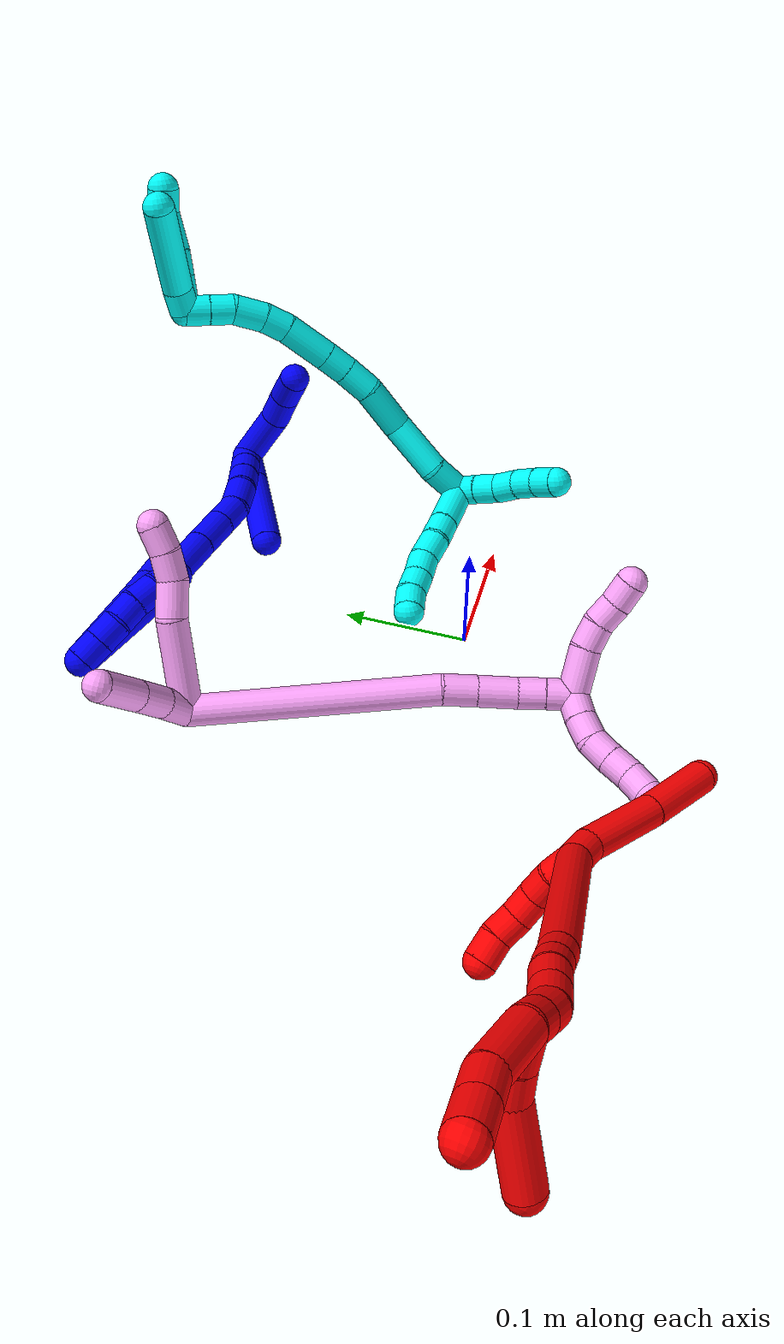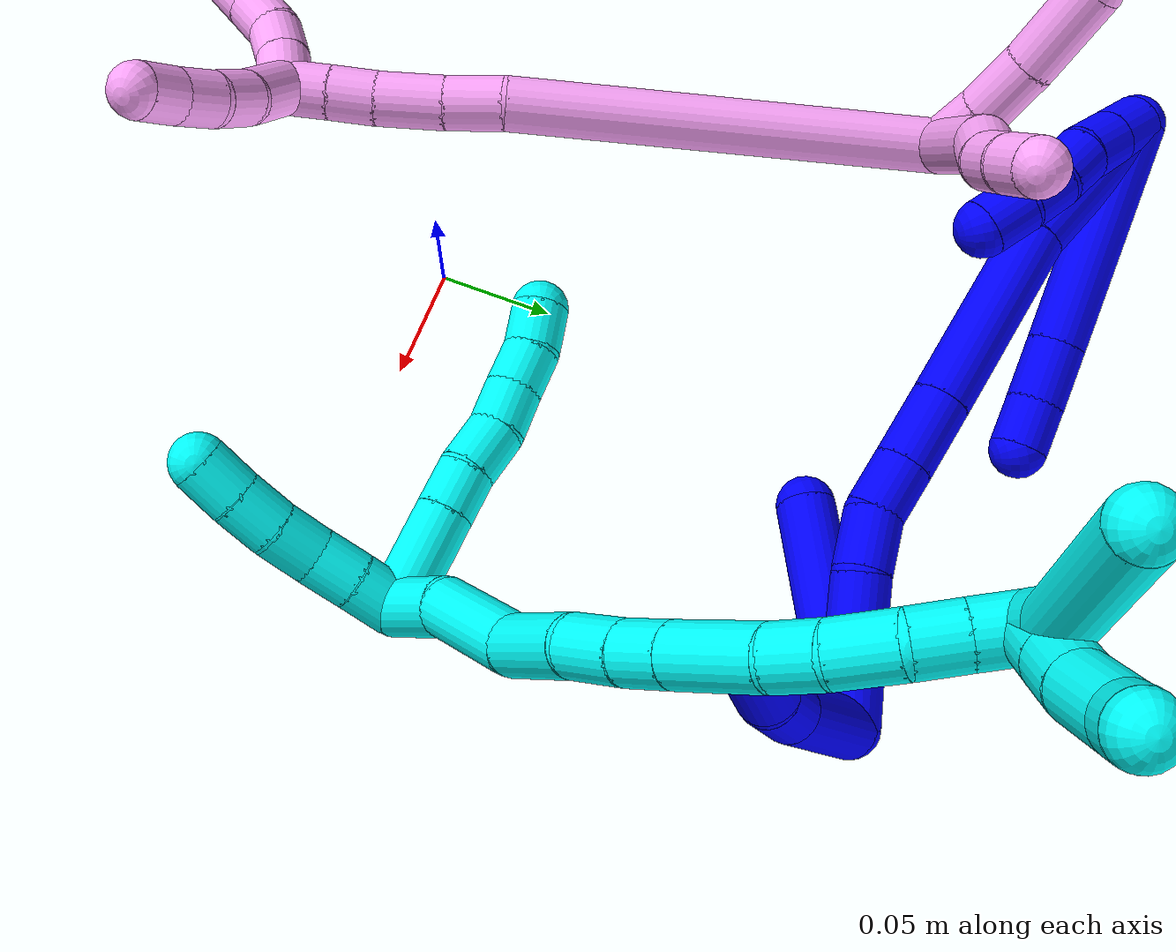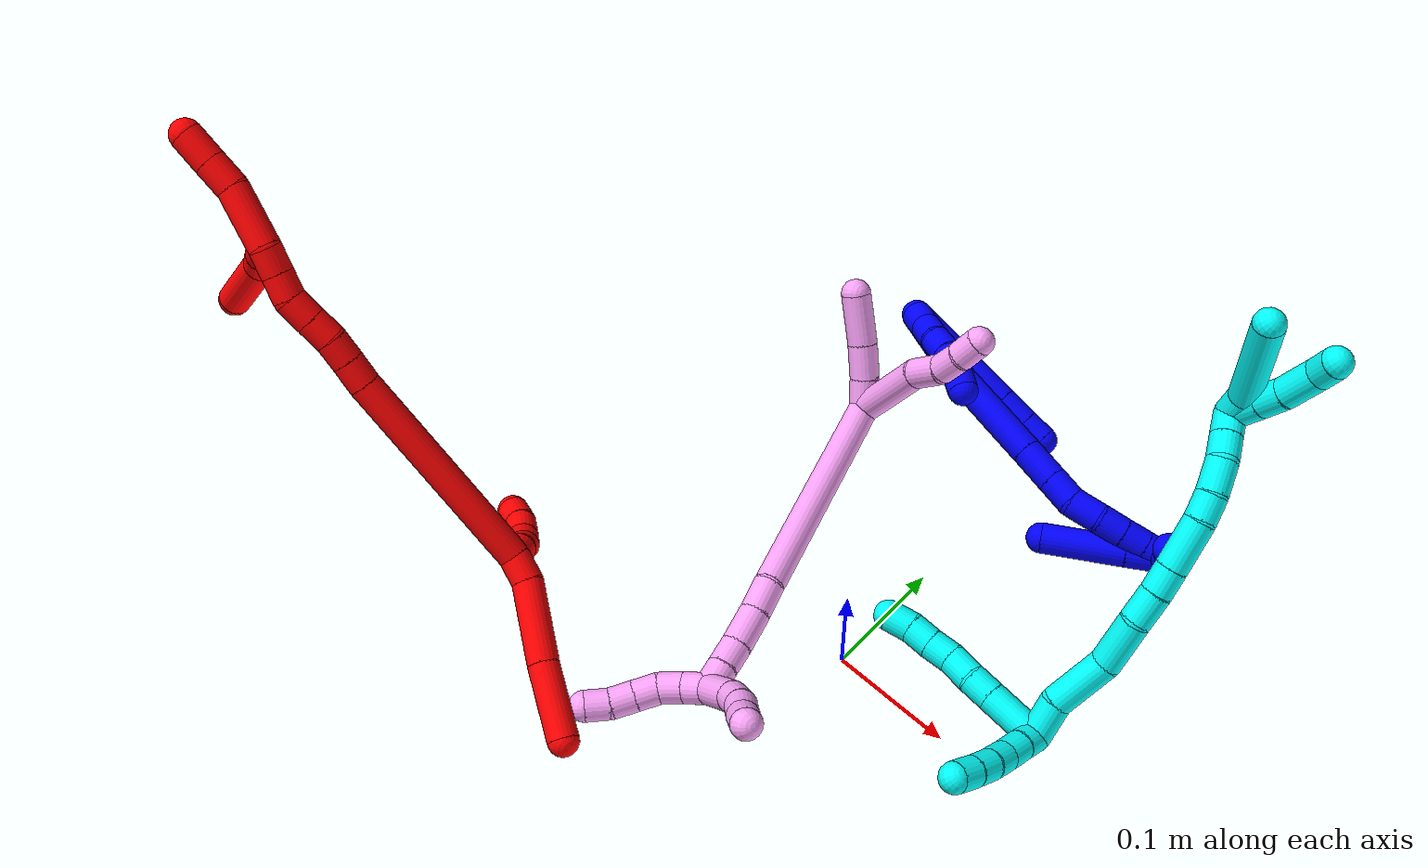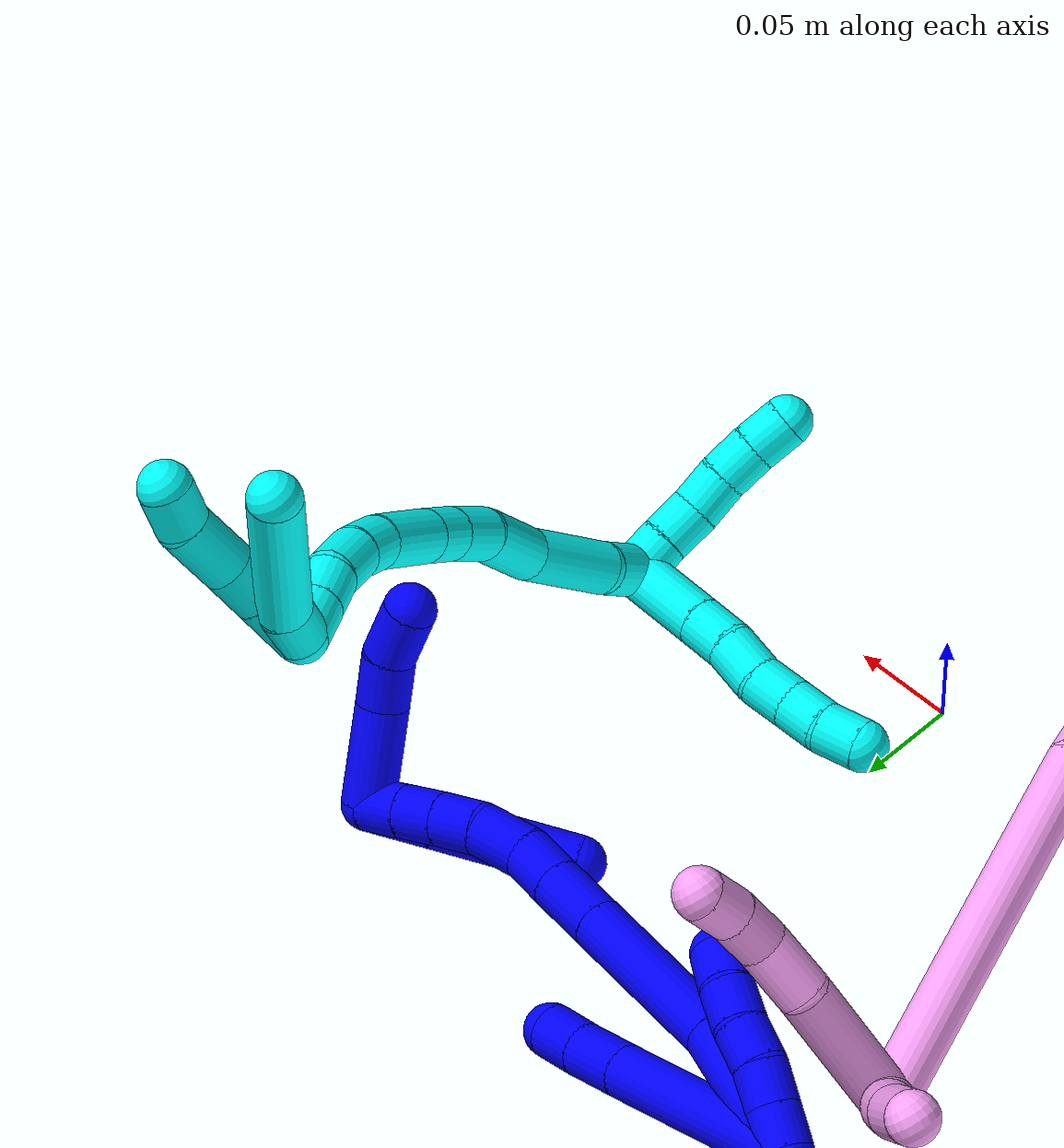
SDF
<sdf version="1.7">
 <world name="default">
  <plugin name="TubeGeneratorPlugin" filename="libtube_generator_plugin.so"/>
  <model name="photoneo_s_sensor">
   <static>1</static>
   <pose>0 0 2 1.57079 1.57079 3.14159</pose>
   <link name="link">
    <inertial><mass>0.1</mass></inertial>
    <sensor name="sensor" type="depth">
     <update_rate>30</update_rate>
     <camera>
      <horizontal_fov>1.22</horizontal_fov>
      <image><width>1920</width><height>1200</height><format>B8G8R8</format></image>
      <clip><near>0.1</near><far>4</far></clip>
      <depth_camera><output>points</output></depth_camera>
     </camera>
     <plugin name="camera_plugin" filename="libgazebo_ros_depth_camera.so">
      <baseline>0.2</baseline>
      <alwaysOn>1</alwaysOn>
      <updateRate>0.0</updateRate>
      <cameraName>camera_ir</cameraName>
      <imageTopicName>/camera/color/image_raw</imageTopicName>
      <cameraInfoTopicName>/camera/color/camera_info</cameraInfoTopicName>
      <depthImageTopicName>/camera/depth/image_raw</depthImageTopicName>
      <depthImageCameraInfoTopicName>/camera/depth/camera_info</depthImageCameraInfoTopicName>
      <pointCloudTopicName>/camera/depth/points</pointCloudTopicName>
      <frameName>fr_optical</frameName>
      <pointCloudCutoff>0.1</pointCloudCutoff>
      <pointCloudCutoffMax>2.0</pointCloudCutoffMax>
      <distortionK1>0</distortionK1>
      <distortionK2>0</distortionK2>
      <distortionK3>0</distortionK3>
      <distortionT1>0</distortionT1>
      <distortionT2>0</distortionT2>
      <CxPrime>0</CxPrime>
      <Cx>0</Cx>
      <Cy>0</Cy>
      <focalLength>0</focalLength>
      <hackBaseline>0</hackBaseline>
     </plugin>
    </sensor>
   </link>
  </model>
  <gravity>0 0 -9.8</gravity>
  <magnetic_field>6e-06 2.3e-05 -4.2e-05</magnetic_field>
  <atmosphere type="adiabatic"/>
  <physics name="default_physics" default="0" type="ode">
   <max_step_size>0.003</max_step_size>
   <real_time_factor>1</real_time_factor>
   <real_time_update_rate>1000</real_time_update_rate>
   <max_contacts>10000</max_contacts>
   <ode>
    <solver>
     <type>quick</type>
     <iters>100</iters>
     <sor>1.3</sor>
     <use_dynamic_moi_rescaling>0</use_dynamic_moi_rescaling>
    </solver>
    <constraints>
     <contact_max_correcting_vel>0</contact_max_correcting_vel>
     <contact_surface_layer>0.001</contact_surface_layer>
     <cfm>0</cfm>
     <erp>0.2</erp>
    </constraints>
   </ode>
  </physics>
  <scene><ambient>0.4 0.4 0.4 1</ambient><background>0.7 0.7 0.7 1</background><shadows>0</shadows></scene>
  <audio><device>default</device></audio>
  <spherical_coordinates>
   <surface_model>EARTH_WGS84</surface_model>
   <latitude_deg>0</latitude_deg>
   <longitude_deg>0</longitude_deg>
   <elevation>0</elevation>
   <heading_deg>0</heading_deg>
  </spherical_coordinates>
  <model name="bin">
   <static>1</static>
   <link name="bottom">
    <collision name="collision-bottom">
     <pose>0 0 -0.01 0 -0 0</pose>
     <geometry><box><size>0.8 0.6 0.02</size></box></geometry>
     <surface>
      <friction><ode><mu>100</mu><mu2>100</mu2></ode></friction>
      <contact><collide_bitmask>65535</collide_bitmask></contact>
     </surface>
    </collision>
   </link>
   <link name="west_wall">
    <collision name="collision-west_wall">
     <pose>-0.41 0 0.1 0 -0 0</pose>
     <geometry><box><size>0.02 0.6 0.2</size></box></geometry>
     <surface>
      <friction><ode><mu>100</mu><mu2>100</mu2></ode></friction>
      <contact><collide_bitmask>65535</collide_bitmask></contact>
     </surface>
    </collision>
   </link>
   <link name="east_wall">
    <collision name="collision-east_wall">
     <pose>0.41 0 0.1 0 -0 0</pose>
     <geometry><box><size>0.02 0.6 0.2</size></box></geometry>
     <surface>
      <friction><ode><mu>100</mu><mu2>100</mu2></ode></friction>
      <contact><collide_bitmask>65535</collide_bitmask></contact>
     </surface>
    </collision>
   </link>
   <link name="south_wall">
    <collision name="collision-south_wall">
     <pose>0 -0.31 0.1 0 -0 0</pose>
     <geometry><box><size>0.8 0.02 0.2</size></box></geometry>
     <surface>
      <friction><ode><mu>100</mu><mu2>100</mu2></ode></friction>
      <contact><collide_bitmask>65535</collide_bitmask></contact>
     </surface>
    </collision>
   </link>
   <link name="north_wall">
    <collision name="collision-north_wall">
     <pose>0 0.31 0.1 0 -0 0</pose>
     <geometry><box><size>0.8 0.02 0.2</size></box></geometry>
     <surface>
      <friction><ode><mu>100</mu><mu2>100</mu2></ode></friction>
      <contact><collide_bitmask>65535</collide_bitmask></contact>
     </surface>
    </collision>
   </link>
  </model>
  <model name="1">
   <static>0</static>
   <link name="1">
    <collision name="collision-cylinder-e_1_2_8">
     <pose>0.039856 -0.010253 -0.030038 2.81266 0.898281 2.47837</pose>
     <geometry><cylinder><radius>0.0125</radius><length>0.1019</length></cylinder></geometry>
     <surface>
      <friction><ode><mu>1.16</mu><mu2>1.16</mu2><slip1>0</slip1><slip2>0</slip2></ode></friction>
      <contact><ode><kp>1e+06</kp><kd>1</kd><max_vel>0</max_vel><min_depth>0.001</min_depth></ode></contact>
     </surface>
    </collision>
    <visual name="visual-cylinder-e_1_2_8">
     <pose>0.039856 -0.010253 -0.030038 2.81266 0.898281 2.47837</pose>
     <geometry><cylinder><radius>0.0125</radius><length>0.1019</length></cylinder></geometry>
     <material><ambient>0 0 1 1</ambient></material>
    </visual>
    <collision name="collision-cylinder-e_2_8_9">
     <pose>0.090175 -0.023431 -0.068098 2.79196 0.886331 2.42915</pose>
     <geometry><cylinder><radius>0.0125</radius><length>0.027009</length></cylinder></geometry>
     <surface>
      <friction><ode><mu>1.16</mu><mu2>1.16</mu2><slip1>0</slip1><slip2>0</slip2></ode></friction>
      <contact><ode><kp>1e+06</kp><kd>1</kd><max_vel>0</max_vel><min_depth>0.001</min_depth></ode></contact>
     </surface>
    </collision>
    <visual name="visual-cylinder-e_2_8_9">
     <pose>0.090175 -0.023431 -0.068098 2.79196 0.886331 2.42915</pose>
     <geometry><cylinder><radius>0.0125</radius><length>0.027009</length></cylinder></geometry>
     <material><ambient>0 0 1 1</ambient></material>
    </visual>
    <collision name="collision-cylinder-e_3_9_6">
     <pose>0.10848 -0.029198 -0.082572 2.72666 0.838524 2.25911</pose>
     <geometry><cylinder><radius>0.0125</radius><length>0.021091</length></cylinder></geometry>
     <surface>
      <friction><ode><mu>1.16</mu><mu2>1.16</mu2><slip1>0</slip1><slip2>0</slip2></ode></friction>
      <contact><ode><kp>1e+06</kp><kd>1</kd><max_vel>0</max_vel><min_depth>0.001</min_depth></ode></contact>
     </surface>
    </collision>
    <visual name="visual-cylinder-e_3_9_6">
     <pose>0.10848 -0.029198 -0.082572 2.72666 0.838524 2.25911</pose>
     <geometry><cylinder><radius>0.0125</radius><length>0.021091</length></cylinder></geometry>
     <material><ambient>0 0 1 1</ambient></material>
    </visual>
    <collision name="collision-cylinder-e_1_2_10">
     <pose>0.000831 -0.005273 -0.008456 2.58401 0.083176 0.288722</pose>
     <geometry><cylinder><radius>0.0125</radius><length>0.02</length></cylinder></geometry>
     <surface>
      <friction><ode><mu>1.16</mu><mu2>1.16</mu2><slip1>0</slip1><slip2>0</slip2></ode></friction>
      <contact><ode><kp>1e+06</kp><kd>1</kd><max_vel>0</max_vel><min_depth>0.001</min_depth></ode></contact>
     </surface>
    </collision>
    <visual name="visual-cylinder-e_1_2_10">
     <pose>0.000831 -0.005273 -0.008456 2.58401 0.083176 0.288722</pose>
     <geometry><cylinder><radius>0.0125</radius><length>0.02</length></cylinder></geometry>
     <material><ambient>0 0 1 1</ambient></material>
    </visual>
    <collision name="collision-cylinder-e_2_10_11">
     <pose>0.002433 -0.015862 -0.025347 2.5792 0.077188 0.265785</pose>
     <geometry><cylinder><radius>0.0125</radius><length>0.02</length></cylinder></geometry>
     <surface>
      <friction><ode><mu>1.16</mu><mu2>1.16</mu2><slip1>0</slip1><slip2>0</slip2></ode></friction>
      <contact><ode><kp>1e+06</kp><kd>1</kd><max_vel>0</max_vel><min_depth>0.001</min_depth></ode></contact>
     </surface>
    </collision>
    <visual name="visual-cylinder-e_2_10_11">
     <pose>0.002433 -0.015862 -0.025347 2.5792 0.077188 0.265785</pose>
     <geometry><cylinder><radius>0.0125</radius><length>0.02</length></cylinder></geometry>
     <material><ambient>0 0 1 1</ambient></material>
    </visual>
    <collision name="collision-cylinder-e_3_11_12">
     <pose>0.005907 -0.026159 -0.042021 2.59793 0.273745 0.91791</pose>
     <geometry><cylinder><radius>0.0125</radius><length>0.02</length></cylinder></geometry>
     <surface>
      <friction><ode><mu>1.16</mu><mu2>1.16</mu2><slip1>0</slip1><slip2>0</slip2></ode></friction>
      <contact><ode><kp>1e+06</kp><kd>1</kd><max_vel>0</max_vel><min_depth>0.001</min_depth></ode></contact>
     </surface>
    </collision>
    <visual name="visual-cylinder-e_3_11_12">
     <pose>0.005907 -0.026159 -0.042021 2.59793 0.273745 0.91791</pose>
     <geometry><cylinder><radius>0.0125</radius><length>0.02</length></cylinder></geometry>
     <material><ambient>0 0 1 1</ambient></material>
    </visual>
    <collision name="collision-cylinder-e_4_12_13">
     <pose>0.010913 -0.034631 -0.059344 2.77456 0.232372 1.12267</pose>
     <geometry><cylinder><radius>0.0125</radius><length>0.02</length></cylinder></geometry>
     <surface>
      <friction><ode><mu>1.16</mu><mu2>1.16</mu2><slip1>0</slip1><slip2>0</slip2></ode></friction>
      <contact><ode><kp>1e+06</kp><kd>1</kd><max_vel>0</max_vel><min_depth>0.001</min_depth></ode></contact>
     </surface>
    </collision>
    <visual name="visual-cylinder-e_4_12_13">
     <pose>0.010913 -0.034631 -0.059344 2.77456 0.232372 1.12267</pose>
     <geometry><cylinder><radius>0.0125</radius><length>0.02</length></cylinder></geometry>
     <material><ambient>0 0 1 1</ambient></material>
    </visual>
    <collision name="collision-cylinder-e_5_13_5">
     <pose>0.015724 -0.039882 -0.077946 2.95891 0.253521 1.89521</pose>
     <geometry><cylinder><radius>0.0125</radius><length>0.02</length></cylinder></geometry>
     <surface>
      <friction><ode><mu>1.16</mu><mu2>1.16</mu2><slip1>0</slip1><slip2>0</slip2></ode></friction>
      <contact><ode><kp>1e+06</kp><kd>1</kd><max_vel>0</max_vel><min_depth>0.001</min_depth></ode></contact>
     </surface>
    </collision>
    <visual name="visual-cylinder-e_5_13_5">
     <pose>0.015724 -0.039882 -0.077946 2.95891 0.253521 1.89521</pose>
     <geometry><cylinder><radius>0.0125</radius><length>0.02</length></cylinder></geometry>
     <material><ambient>0 0 1 1</ambient></material>
    </visual>
    <collision name="collision-cylinder-e_1_2_14">
     <pose>0.015461 -0.011699 -0.030374 2.77393 0.443437 1.76223</pose>
     <geometry><cylinder><radius>0.0125</radius><length>0.072069</length></cylinder></geometry>
     <surface>
      <friction><ode><mu>1.16</mu><mu2>1.16</mu2><slip1>0</slip1><slip2>0</slip2></ode></friction>
      <contact><ode><kp>1e+06</kp><kd>1</kd><max_vel>0</max_vel><min_depth>0.001</min_depth></ode></contact>
     </surface>
    </collision>
    <visual name="visual-cylinder-e_1_2_14">
     <pose>0.015461 -0.011699 -0.030374 2.77393 0.443437 1.76223</pose>
     <geometry><cylinder><radius>0.0125</radius><length>0.072069</length></cylinder></geometry>
     <material><ambient>0 0 1 1</ambient></material>
    </visual>
    <collision name="collision-cylinder-e_2_14_15">
     <pose>0.056139 -0.037064 -0.091601 2.72463 0.641791 2.00797</pose>
     <geometry><cylinder><radius>0.0125</radius><length>0.08425</length></cylinder></geometry>
     <surface>
      <friction><ode><mu>1.16</mu><mu2>1.16</mu2><slip1>0</slip1><slip2>0</slip2></ode></friction>
      <contact><ode><kp>1e+06</kp><kd>1</kd><max_vel>0</max_vel><min_depth>0.001</min_depth></ode></contact>
     </surface>
    </collision>
    <visual name="visual-cylinder-e_2_14_15">
     <pose>0.056139 -0.037064 -0.091601 2.72463 0.641791 2.00797</pose>
     <geometry><cylinder><radius>0.0125</radius><length>0.08425</length></cylinder></geometry>
     <material><ambient>0 0 1 1</ambient></material>
    </visual>
    <collision name="collision-cylinder-e_3_15_16">
     <pose>0.090886 -0.055781 -0.134206 2.73572 0.640292 2.03071</pose>
     <geometry><cylinder><radius>0.0125</radius><length>0.031904</length></cylinder></geometry>
     <surface>
      <friction><ode><mu>1.16</mu><mu2>1.16</mu2><slip1>0</slip1><slip2>0</slip2></ode></friction>
      <contact><ode><kp>1e+06</kp><kd>1</kd><max_vel>0</max_vel><min_depth>0.001</min_depth></ode></contact>
     </surface>
    </collision>
    <visual name="visual-cylinder-e_3_15_16">
     <pose>0.090886 -0.055781 -0.134206 2.73572 0.640292 2.03071</pose>
     <geometry><cylinder><radius>0.0125</radius><length>0.031904</length></cylinder></geometry>
     <material><ambient>0 0 1 1</ambient></material>
    </visual>
    <collision name="collision-cylinder-e_4_16_17">
     <pose>0.107459 -0.064747 -0.154901 2.72882 0.624962 1.99156</pose>
     <geometry><cylinder><radius>0.0125</radius><length>0.024073</length></cylinder></geometry>
     <surface>
      <friction><ode><mu>1.16</mu><mu2>1.16</mu2><slip1>0</slip1><slip2>0</slip2></ode></friction>
      <contact><ode><kp>1e+06</kp><kd>1</kd><max_vel>0</max_vel><min_depth>0.001</min_depth></ode></contact>
     </surface>
    </collision>
    <visual name="visual-cylinder-e_4_16_17">
     <pose>0.107459 -0.064747 -0.154901 2.72882 0.624962 1.99156</pose>
     <geometry><cylinder><radius>0.0125</radius><length>0.024073</length></cylinder></geometry>
     <material><ambient>0 0 1 1</ambient></material>
    </visual>
    <collision name="collision-cylinder-e_5_17_18">
     <pose>0.123925 -0.074784 -0.170274 2.38088 0.81521 1.64762</pose>
     <geometry><cylinder><radius>0.0125</radius><length>0.025895</length></cylinder></geometry>
     <surface>
      <friction><ode><mu>1.16</mu><mu2>1.16</mu2><slip1>0</slip1><slip2>0</slip2></ode></friction>
      <contact><ode><kp>1e+06</kp><kd>1</kd><max_vel>0</max_vel><min_depth>0.001</min_depth></ode></contact>
     </surface>
    </collision>
    <visual name="visual-cylinder-e_5_17_18">
     <pose>0.123925 -0.074784 -0.170274 2.38088 0.81521 1.64762</pose>
     <geometry><cylinder><radius>0.0125</radius><length>0.025895</length></cylinder></geometry>
     <material><ambient>0 0 1 1</ambient></material>
    </visual>
    <collision name="collision-cylinder-e_6_18_19">
     <pose>0.142647 -0.084392 -0.180827 2.43949 1.04462 2.00836</pose>
     <geometry><cylinder><radius>0.0125</radius><length>0.021506</length></cylinder></geometry>
     <surface>
      <friction><ode><mu>1.16</mu><mu2>1.16</mu2><slip1>0</slip1><slip2>0</slip2></ode></friction>
      <contact><ode><kp>1e+06</kp><kd>1</kd><max_vel>0</max_vel><min_depth>0.001</min_depth></ode></contact>
     </surface>
    </collision>
    <visual name="visual-cylinder-e_6_18_19">
     <pose>0.142647 -0.084392 -0.180827 2.43949 1.04462 2.00836</pose>
     <geometry><cylinder><radius>0.0125</radius><length>0.021506</length></cylinder></geometry>
     <material><ambient>0 0 1 1</ambient></material>
    </visual>
    <collision name="collision-cylinder-e_7_19_20">
     <pose>0.16081 -0.091044 -0.188552 2.42083 1.07503 2.01406</pose>
     <geometry><cylinder><radius>0.0125</radius><length>0.020155</length></cylinder></geometry>
     <surface>
      <friction><ode><mu>1.16</mu><mu2>1.16</mu2><slip1>0</slip1><slip2>0</slip2></ode></friction>
      <contact><ode><kp>1e+06</kp><kd>1</kd><max_vel>0</max_vel><min_depth>0.001</min_depth></ode></contact>
     </surface>
    </collision>
    <visual name="visual-cylinder-e_7_19_20">
     <pose>0.16081 -0.091044 -0.188552 2.42083 1.07503 2.01406</pose>
     <geometry><cylinder><radius>0.0125</radius><length>0.020155</length></cylinder></geometry>
     <material><ambient>0 0 1 1</ambient></material>
    </visual>
    <collision name="collision-cylinder-e_8_20_1">
     <pose>0.178571 -0.097303 -0.195723 2.42705 1.08265 2.03034</pose>
     <geometry><cylinder><radius>0.0125</radius><length>0.020148</length></cylinder></geometry>
     <surface>
      <friction><ode><mu>1.16</mu><mu2>1.16</mu2><slip1>0</slip1><slip2>0</slip2></ode></friction>
      <contact><ode><kp>1e+06</kp><kd>1</kd><max_vel>0</max_vel><min_depth>0.001</min_depth></ode></contact>
     </surface>
    </collision>
    <visual name="visual-cylinder-e_8_20_1">
     <pose>0.178571 -0.097303 -0.195723 2.42705 1.08265 2.03034</pose>
     <geometry><cylinder><radius>0.0125</radius><length>0.020148</length></cylinder></geometry>
     <material><ambient>0 0 1 1</ambient></material>
    </visual>
    <collision name="collision-cylinder-e_1_1_21">
     <pose>0.175845 -0.090026 -0.197024 -1.35554 -0.830553 0.682123</pose>
     <geometry><cylinder><radius>0.0125</radius><length>0.031487</length></cylinder></geometry>
     <surface>
      <friction><ode><mu>1.16</mu><mu2>1.16</mu2><slip1>0</slip1><slip2>0</slip2></ode></friction>
      <contact><ode><kp>1e+06</kp><kd>1</kd><max_vel>0</max_vel><min_depth>0.001</min_depth></ode></contact>
     </surface>
    </collision>
    <visual name="visual-cylinder-e_1_1_21">
     <pose>0.175845 -0.090026 -0.197024 -1.35554 -0.830553 0.682123</pose>
     <geometry><cylinder><radius>0.0125</radius><length>0.031487</length></cylinder></geometry>
     <material><ambient>0 0 1 1</ambient></material>
    </visual>
    <collision name="collision-cylinder-e_2_21_4">
     <pose>0.13889 -0.057189 -0.189534 -1.34239 -0.832251 0.675103</pose>
     <geometry><cylinder><radius>0.0125</radius><length>0.068513</length></cylinder></geometry>
     <surface>
      <friction><ode><mu>1.16</mu><mu2>1.16</mu2><slip1>0</slip1><slip2>0</slip2></ode></friction>
      <contact><ode><kp>1e+06</kp><kd>1</kd><max_vel>0</max_vel><min_depth>0.001</min_depth></ode></contact>
     </surface>
    </collision>
    <visual name="visual-cylinder-e_2_21_4">
     <pose>0.13889 -0.057189 -0.189534 -1.34239 -0.832251 0.675103</pose>
     <geometry><cylinder><radius>0.0125</radius><length>0.068513</length></cylinder></geometry>
     <material><ambient>0 0 1 1</ambient></material>
    </visual>
    <collision name="collision-cylinder-e_1_1_22">
     <pose>0.174116 -0.115408 -0.212159 2.27956 -0.594014 -1.17447</pose>
     <geometry><cylinder><radius>0.0125</radius><length>0.047712</length></cylinder></geometry>
     <surface>
      <friction><ode><mu>1.16</mu><mu2>1.16</mu2><slip1>0</slip1><slip2>0</slip2></ode></friction>
      <contact><ode><kp>1e+06</kp><kd>1</kd><max_vel>0</max_vel><min_depth>0.001</min_depth></ode></contact>
     </surface>
    </collision>
    <visual name="visual-cylinder-e_1_1_22">
     <pose>0.174116 -0.115408 -0.212159 2.27956 -0.594014 -1.17447</pose>
     <geometry><cylinder><radius>0.0125</radius><length>0.047712</length></cylinder></geometry>
     <material><ambient>0 0 1 1</ambient></material>
    </visual>
    <collision name="collision-cylinder-e_2_22_23">
     <pose>0.152969 -0.139162 -0.229454 2.03939 -0.671785 -1.03316</pose>
     <geometry><cylinder><radius>0.0125</radius><length>0.025049</length></cylinder></geometry>
     <surface>
      <friction><ode><mu>1.16</mu><mu2>1.16</mu2><slip1>0</slip1><slip2>0</slip2></ode></friction>
      <contact><ode><kp>1e+06</kp><kd>1</kd><max_vel>0</max_vel><min_depth>0.001</min_depth></ode></contact>
     </surface>
    </collision>
    <visual name="visual-cylinder-e_2_22_23">
     <pose>0.152969 -0.139162 -0.229454 2.03939 -0.671785 -1.03316</pose>
     <geometry><cylinder><radius>0.0125</radius><length>0.025049</length></cylinder></geometry>
     <material><ambient>0 0 1 1</ambient></material>
    </visual>
    <collision name="collision-cylinder-e_3_23_3">
     <pose>0.134139 -0.155356 -0.236754 1.9389 -0.944623 -1.28006</pose>
     <geometry><cylinder><radius>0.0125</radius><length>0.027239</length></cylinder></geometry>
     <surface>
      <friction><ode><mu>1.16</mu><mu2>1.16</mu2><slip1>0</slip1><slip2>0</slip2></ode></friction>
      <contact><ode><kp>1e+06</kp><kd>1</kd><max_vel>0</max_vel><min_depth>0.001</min_depth></ode></contact>
     </surface>
    </collision>
    <visual name="visual-cylinder-e_3_23_3">
     <pose>0.134139 -0.155356 -0.236754 1.9389 -0.944623 -1.28006</pose>
     <geometry><cylinder><radius>0.0125</radius><length>0.027239</length></cylinder></geometry>
     <material><ambient>0 0 1 1</ambient></material>
    </visual>
    <collision name="collision-sphere-3">
     <pose>0.123103 -0.162803 -0.239626 0 -0 0</pose>
     <geometry><sphere><radius>0.0125</radius></sphere></geometry>
     <surface>
      <friction><ode><mu>1.16</mu><mu2>1.16</mu2><slip1>0</slip1><slip2>0</slip2></ode></friction>
      <contact><ode><kp>1e+06</kp><kd>1</kd><max_vel>0</max_vel><min_depth>0.001</min_depth></ode></contact>
     </surface>
    </collision>
    <visual name="visual-sphere-3">
     <pose>0.123103 -0.162803 -0.239626 0 -0 0</pose>
     <geometry><sphere><radius>0.0125</radius></sphere></geometry>
     <material><ambient>0 0 1 1</ambient></material>
    </visual>
    <collision name="collision-sphere-23">
     <pose>0.145174 -0.147909 -0.233882 0 -0 0</pose>
     <geometry><sphere><radius>0.0125</radius></sphere></geometry>
     <surface>
      <friction><ode><mu>1.16</mu><mu2>1.16</mu2><slip1>0</slip1><slip2>0</slip2></ode></friction>
      <contact><ode><kp>1e+06</kp><kd>1</kd><max_vel>0</max_vel><min_depth>0.001</min_depth></ode></contact>
     </surface>
    </collision>
    <visual name="visual-sphere-23">
     <pose>0.145174 -0.147909 -0.233882 0 -0 0</pose>
     <geometry><sphere><radius>0.0125</radius></sphere></geometry>
     <material><ambient>0 0 1 1</ambient></material>
    </visual>
    <collision name="collision-sphere-22">
     <pose>0.160765 -0.130416 -0.225027 0 -0 0</pose>
     <geometry><sphere><radius>0.0125</radius></sphere></geometry>
     <surface>
      <friction><ode><mu>1.16</mu><mu2>1.16</mu2><slip1>0</slip1><slip2>0</slip2></ode></friction>
      <contact><ode><kp>1e+06</kp><kd>1</kd><max_vel>0</max_vel><min_depth>0.001</min_depth></ode></contact>
     </surface>
    </collision>
    <visual name="visual-sphere-22">
     <pose>0.160765 -0.130416 -0.225027 0 -0 0</pose>
     <geometry><sphere><radius>0.0125</radius></sphere></geometry>
     <material><ambient>0 0 1 1</ambient></material>
    </visual>
    <collision name="collision-sphere-4">
     <pose>0.11356 -0.034726 -0.184312 0 -0 0</pose>
     <geometry><sphere><radius>0.0125</radius></sphere></geometry>
     <surface>
      <friction><ode><mu>1.16</mu><mu2>1.16</mu2><slip1>0</slip1><slip2>0</slip2></ode></friction>
      <contact><ode><kp>1e+06</kp><kd>1</kd><max_vel>0</max_vel><min_depth>0.001</min_depth></ode></contact>
     </surface>
    </collision>
    <visual name="visual-sphere-4">
     <pose>0.11356 -0.034726 -0.184312 0 -0 0</pose>
     <geometry><sphere><radius>0.0125</radius></sphere></geometry>
     <material><ambient>0 0 1 1</ambient></material>
    </visual>
    <collision name="collision-sphere-21">
     <pose>0.164221 -0.079652 -0.194755 0 -0 0</pose>
     <geometry><sphere><radius>0.0125</radius></sphere></geometry>
     <surface>
      <friction><ode><mu>1.16</mu><mu2>1.16</mu2><slip1>0</slip1><slip2>0</slip2></ode></friction>
      <contact><ode><kp>1e+06</kp><kd>1</kd><max_vel>0</max_vel><min_depth>0.001</min_depth></ode></contact>
     </surface>
    </collision>
    <visual name="visual-sphere-21">
     <pose>0.164221 -0.079652 -0.194755 0 -0 0</pose>
     <geometry><sphere><radius>0.0125</radius></sphere></geometry>
     <material><ambient>0 0 1 1</ambient></material>
    </visual>
    <collision name="collision-sphere-1">
     <pose>0.187468 -0.100399 -0.199292 0 -0 0</pose>
     <geometry><sphere><radius>0.0125</radius></sphere></geometry>
     <surface>
      <friction><ode><mu>1.16</mu><mu2>1.16</mu2><slip1>0</slip1><slip2>0</slip2></ode></friction>
      <contact><ode><kp>1e+06</kp><kd>1</kd><max_vel>0</max_vel><min_depth>0.001</min_depth></ode></contact>
     </surface>
    </collision>
    <visual name="visual-sphere-1">
     <pose>0.187468 -0.100399 -0.199292 0 -0 0</pose>
     <geometry><sphere><radius>0.0125</radius></sphere></geometry>
     <material><ambient>0 0 1 1</ambient></material>
    </visual>
    <collision name="collision-sphere-11">
     <pose>0.003204 -0.021179 -0.033781 0 -0 0</pose>
     <geometry><sphere><radius>0.0125</radius></sphere></geometry>
     <surface>
      <friction><ode><mu>1.16</mu><mu2>1.16</mu2><slip1>0</slip1><slip2>0</slip2></ode></friction>
      <contact><ode><kp>1e+06</kp><kd>1</kd><max_vel>0</max_vel><min_depth>0.001</min_depth></ode></contact>
     </surface>
    </collision>
    <visual name="visual-sphere-11">
     <pose>0.003204 -0.021179 -0.033781 0 -0 0</pose>
     <geometry><sphere><radius>0.0125</radius></sphere></geometry>
     <material><ambient>0 0 1 1</ambient></material>
    </visual>
    <collision name="collision-sphere-10">
     <pose>0.001662 -0.010546 -0.016912 0 -0 0</pose>
     <geometry><sphere><radius>0.0125</radius></sphere></geometry>
     <surface>
      <friction><ode><mu>1.16</mu><mu2>1.16</mu2><slip1>0</slip1><slip2>0</slip2></ode></friction>
      <contact><ode><kp>1e+06</kp><kd>1</kd><max_vel>0</max_vel><min_depth>0.001</min_depth></ode></contact>
     </surface>
    </collision>
    <visual name="visual-sphere-10">
     <pose>0.001662 -0.010546 -0.016912 0 -0 0</pose>
     <geometry><sphere><radius>0.0125</radius></sphere></geometry>
     <material><ambient>0 0 1 1</ambient></material>
    </visual>
    <collision name="collision-sphere-6">
     <pose>0.116322 -0.03204 -0.089024 0 -0 0</pose>
     <geometry><sphere><radius>0.0125</radius></sphere></geometry>
     <surface>
      <friction><ode><mu>1.16</mu><mu2>1.16</mu2><slip1>0</slip1><slip2>0</slip2></ode></friction>
      <contact><ode><kp>1e+06</kp><kd>1</kd><max_vel>0</max_vel><min_depth>0.001</min_depth></ode></contact>
     </surface>
    </collision>
    <visual name="visual-sphere-6">
     <pose>0.116322 -0.03204 -0.089024 0 -0 0</pose>
     <geometry><sphere><radius>0.0125</radius></sphere></geometry>
     <material><ambient>0 0 1 1</ambient></material>
    </visual>
    <collision name="collision-sphere-9">
     <pose>0.100637 -0.026355 -0.076119 0 -0 0</pose>
     <geometry><sphere><radius>0.0125</radius></sphere></geometry>
     <surface>
      <friction><ode><mu>1.16</mu><mu2>1.16</mu2><slip1>0</slip1><slip2>0</slip2></ode></friction>
      <contact><ode><kp>1e+06</kp><kd>1</kd><max_vel>0</max_vel><min_depth>0.001</min_depth></ode></contact>
     </surface>
    </collision>
    <visual name="visual-sphere-9">
     <pose>0.100637 -0.026355 -0.076119 0 -0 0</pose>
     <geometry><sphere><radius>0.0125</radius></sphere></geometry>
     <material><ambient>0 0 1 1</ambient></material>
    </visual>
    <collision name="collision-sphere-2">
     <geometry><sphere><radius>0.0125</radius></sphere></geometry>
     <surface>
      <friction><ode><mu>1.16</mu><mu2>1.16</mu2><slip1>0</slip1><slip2>0</slip2></ode></friction>
      <contact><ode><kp>1e+06</kp><kd>1</kd><max_vel>0</max_vel><min_depth>0.001</min_depth></ode></contact>
     </surface>
    </collision>
    <visual name="visual-sphere-2">
     <geometry><sphere><radius>0.0125</radius></sphere></geometry>
     <material><ambient>0 0 1 1</ambient></material>
    </visual>
    <collision name="collision-sphere-19">
     <pose>0.151946 -0.08788 -0.184951 0 -0 0</pose>
     <geometry><sphere><radius>0.0125</radius></sphere></geometry>
     <surface>
      <friction><ode><mu>1.16</mu><mu2>1.16</mu2><slip1>0</slip1><slip2>0</slip2></ode></friction>
      <contact><ode><kp>1e+06</kp><kd>1</kd><max_vel>0</max_vel><min_depth>0.001</min_depth></ode></contact>
     </surface>
    </collision>
    <visual name="visual-sphere-19">
     <pose>0.151946 -0.08788 -0.184951 0 -0 0</pose>
     <geometry><sphere><radius>0.0125</radius></sphere></geometry>
     <material><ambient>0 0 1 1</ambient></material>
    </visual>
    <collision name="collision-sphere-8">
     <pose>0.079712 -0.020506 -0.060076 0 -0 0</pose>
     <geometry><sphere><radius>0.0125</radius></sphere></geometry>
     <surface>
      <friction><ode><mu>1.16</mu><mu2>1.16</mu2><slip1>0</slip1><slip2>0</slip2></ode></friction>
      <contact><ode><kp>1e+06</kp><kd>1</kd><max_vel>0</max_vel><min_depth>0.001</min_depth></ode></contact>
     </surface>
    </collision>
    <visual name="visual-sphere-8">
     <pose>0.079712 -0.020506 -0.060076 0 -0 0</pose>
     <geometry><sphere><radius>0.0125</radius></sphere></geometry>
     <material><ambient>0 0 1 1</ambient></material>
    </visual>
    <collision name="collision-sphere-12">
     <pose>0.008611 -0.031139 -0.050261 0 -0 0</pose>
     <geometry><sphere><radius>0.0125</radius></sphere></geometry>
     <surface>
      <friction><ode><mu>1.16</mu><mu2>1.16</mu2><slip1>0</slip1><slip2>0</slip2></ode></friction>
      <contact><ode><kp>1e+06</kp><kd>1</kd><max_vel>0</max_vel><min_depth>0.001</min_depth></ode></contact>
     </surface>
    </collision>
    <visual name="visual-sphere-12">
     <pose>0.008611 -0.031139 -0.050261 0 -0 0</pose>
     <geometry><sphere><radius>0.0125</radius></sphere></geometry>
     <material><ambient>0 0 1 1</ambient></material>
    </visual>
    <collision name="collision-sphere-13">
     <pose>0.013216 -0.038123 -0.068427 0 -0 0</pose>
     <geometry><sphere><radius>0.0125</radius></sphere></geometry>
     <surface>
      <friction><ode><mu>1.16</mu><mu2>1.16</mu2><slip1>0</slip1><slip2>0</slip2></ode></friction>
      <contact><ode><kp>1e+06</kp><kd>1</kd><max_vel>0</max_vel><min_depth>0.001</min_depth></ode></contact>
     </surface>
    </collision>
    <visual name="visual-sphere-13">
     <pose>0.013216 -0.038123 -0.068427 0 -0 0</pose>
     <geometry><sphere><radius>0.0125</radius></sphere></geometry>
     <material><ambient>0 0 1 1</ambient></material>
    </visual>
    <collision name="collision-sphere-5">
     <pose>0.018233 -0.04164 -0.087465 0 -0 0</pose>
     <geometry><sphere><radius>0.0125</radius></sphere></geometry>
     <surface>
      <friction><ode><mu>1.16</mu><mu2>1.16</mu2><slip1>0</slip1><slip2>0</slip2></ode></friction>
      <contact><ode><kp>1e+06</kp><kd>1</kd><max_vel>0</max_vel><min_depth>0.001</min_depth></ode></contact>
     </surface>
    </collision>
    <visual name="visual-sphere-5">
     <pose>0.018233 -0.04164 -0.087465 0 -0 0</pose>
     <geometry><sphere><radius>0.0125</radius></sphere></geometry>
     <material><ambient>0 0 1 1</ambient></material>
    </visual>
    <collision name="collision-sphere-14">
     <pose>0.030921 -0.023399 -0.060748 0 -0 0</pose>
     <geometry><sphere><radius>0.0125</radius></sphere></geometry>
     <surface>
      <friction><ode><mu>1.16</mu><mu2>1.16</mu2><slip1>0</slip1><slip2>0</slip2></ode></friction>
      <contact><ode><kp>1e+06</kp><kd>1</kd><max_vel>0</max_vel><min_depth>0.001</min_depth></ode></contact>
     </surface>
    </collision>
    <visual name="visual-sphere-14">
     <pose>0.030921 -0.023399 -0.060748 0 -0 0</pose>
     <geometry><sphere><radius>0.0125</radius></sphere></geometry>
     <material><ambient>0 0 1 1</ambient></material>
    </visual>
    <collision name="collision-sphere-15">
     <pose>0.081356 -0.05073 -0.122453 0 -0 0</pose>
     <geometry><sphere><radius>0.0125</radius></sphere></geometry>
     <surface>
      <friction><ode><mu>1.16</mu><mu2>1.16</mu2><slip1>0</slip1><slip2>0</slip2></ode></friction>
      <contact><ode><kp>1e+06</kp><kd>1</kd><max_vel>0</max_vel><min_depth>0.001</min_depth></ode></contact>
     </surface>
    </collision>
    <visual name="visual-sphere-15">
     <pose>0.081356 -0.05073 -0.122453 0 -0 0</pose>
     <geometry><sphere><radius>0.0125</radius></sphere></geometry>
     <material><ambient>0 0 1 1</ambient></material>
    </visual>
    <collision name="collision-sphere-16">
     <pose>0.100417 -0.060831 -0.145959 0 -0 0</pose>
     <geometry><sphere><radius>0.0125</radius></sphere></geometry>
     <surface>
      <friction><ode><mu>1.16</mu><mu2>1.16</mu2><slip1>0</slip1><slip2>0</slip2></ode></friction>
      <contact><ode><kp>1e+06</kp><kd>1</kd><max_vel>0</max_vel><min_depth>0.001</min_depth></ode></contact>
     </surface>
    </collision>
    <visual name="visual-sphere-16">
     <pose>0.100417 -0.060831 -0.145959 0 -0 0</pose>
     <geometry><sphere><radius>0.0125</radius></sphere></geometry>
     <material><ambient>0 0 1 1</ambient></material>
    </visual>
    <collision name="collision-sphere-17">
     <pose>0.114501 -0.068663 -0.163843 0 -0 0</pose>
     <geometry><sphere><radius>0.0125</radius></sphere></geometry>
     <surface>
      <friction><ode><mu>1.16</mu><mu2>1.16</mu2><slip1>0</slip1><slip2>0</slip2></ode></friction>
      <contact><ode><kp>1e+06</kp><kd>1</kd><max_vel>0</max_vel><min_depth>0.001</min_depth></ode></contact>
     </surface>
    </collision>
    <visual name="visual-sphere-17">
     <pose>0.114501 -0.068663 -0.163843 0 -0 0</pose>
     <geometry><sphere><radius>0.0125</radius></sphere></geometry>
     <material><ambient>0 0 1 1</ambient></material>
    </visual>
    <collision name="collision-sphere-18">
     <pose>0.133349 -0.080905 -0.176704 0 -0 0</pose>
     <geometry><sphere><radius>0.0125</radius></sphere></geometry>
     <surface>
      <friction><ode><mu>1.16</mu><mu2>1.16</mu2><slip1>0</slip1><slip2>0</slip2></ode></friction>
      <contact><ode><kp>1e+06</kp><kd>1</kd><max_vel>0</max_vel><min_depth>0.001</min_depth></ode></contact>
     </surface>
    </collision>
    <visual name="visual-sphere-18">
     <pose>0.133349 -0.080905 -0.176704 0 -0 0</pose>
     <geometry><sphere><radius>0.0125</radius></sphere></geometry>
     <material><ambient>0 0 1 1</ambient></material>
    </visual>
    <collision name="collision-sphere-20">
     <pose>0.169674 -0.094208 -0.192154 0 -0 0</pose>
     <geometry><sphere><radius>0.0125</radius></sphere></geometry>
     <surface>
      <friction><ode><mu>1.16</mu><mu2>1.16</mu2><slip1>0</slip1><slip2>0</slip2></ode></friction>
      <contact><ode><kp>1e+06</kp><kd>1</kd><max_vel>0</max_vel><min_depth>0.001</min_depth></ode></contact>
     </surface>
    </collision>
    <visual name="visual-sphere-20">
     <pose>0.169674 -0.094208 -0.192154 0 -0 0</pose>
     <geometry><sphere><radius>0.0125</radius></sphere></geometry>
     <material><ambient>0 0 1 1</ambient></material>
    </visual>
    <inertial>
     <pose>0.08639 -0.052743 -0.115161 0 -0 0</pose>
     <mass>0.75</mass>
     <inertia>
      <ixx>8.7e-05</ixx>
      <ixy>0</ixy>
      <ixz>0</ixz>
      <iyy>0.000269</iyy>
      <iyz>0</iyz>
      <izz>-8.6e-05</izz>
     </inertia>
    </inertial>
   </link>
   <pose>-0.149402 0.264881 0.058401 -1.52775 0.640401 0.680712</pose>
  </model>
  <model name="2">
   <static>0</static>
   <link name="2">
    <collision name="collision-cylinder-e_1_2_8">
     <pose>0.005012 -0.005053 -0.008908 2.62558 0.4551 1.44049</pose>
     <geometry><cylinder><radius>0.0125</radius><length>0.022804</length></cylinder></geometry>
     <surface>
      <friction><ode><mu>1.16</mu><mu2>1.16</mu2><slip1>0</slip1><slip2>0</slip2></ode></friction>
      <contact><ode><kp>1e+06</kp><kd>1</kd><max_vel>0</max_vel><min_depth>0.001</min_depth></ode></contact>
     </surface>
    </collision>
    <visual name="visual-cylinder-e_1_2_8">
     <pose>0.005012 -0.005053 -0.008908 2.62558 0.4551 1.44049</pose>
     <geometry><cylinder><radius>0.0125</radius><length>0.022804</length></cylinder></geometry>
     <material><ambient>1 0 0 1</ambient></material>
    </visual>
    <collision name="collision-cylinder-e_2_8_9">
     <pose>0.030383 -0.015754 -0.043342 2.92384 0.661647 2.52532</pose>
     <geometry><cylinder><radius>0.0125</radius><length>0.066271</length></cylinder></geometry>
     <surface>
      <friction><ode><mu>1.16</mu><mu2>1.16</mu2><slip1>0</slip1><slip2>0</slip2></ode></friction>
      <contact><ode><kp>1e+06</kp><kd>1</kd><max_vel>0</max_vel><min_depth>0.001</min_depth></ode></contact>
     </surface>
    </collision>
    <visual name="visual-cylinder-e_2_8_9">
     <pose>0.030383 -0.015754 -0.043342 2.92384 0.661647 2.52532</pose>
     <geometry><cylinder><radius>0.0125</radius><length>0.066271</length></cylinder></geometry>
     <material><ambient>1 0 0 1</ambient></material>
    </visual>
    <collision name="collision-cylinder-e_3_9_6">
     <pose>0.067869 -0.027204 -0.093383 2.90923 0.597089 2.41663</pose>
     <geometry><cylinder><radius>0.0125</radius><length>0.060925</length></cylinder></geometry>
     <surface>
      <friction><ode><mu>1.16</mu><mu2>1.16</mu2><slip1>0</slip1><slip2>0</slip2></ode></friction>
      <contact><ode><kp>1e+06</kp><kd>1</kd><max_vel>0</max_vel><min_depth>0.001</min_depth></ode></contact>
     </surface>
    </collision>
    <visual name="visual-cylinder-e_3_9_6">
     <pose>0.067869 -0.027204 -0.093383 2.90923 0.597089 2.41663</pose>
     <geometry><cylinder><radius>0.0125</radius><length>0.060925</length></cylinder></geometry>
     <material><ambient>1 0 0 1</ambient></material>
    </visual>
    <collision name="collision-cylinder-e_1_2_10">
     <pose>-0.001775 -0.00749 0.006383 0.865005 -0.178467 -0.082562</pose>
     <geometry><cylinder><radius>0.0125</radius><length>0.02</length></cylinder></geometry>
     <surface>
      <friction><ode><mu>1.16</mu><mu2>1.16</mu2><slip1>0</slip1><slip2>0</slip2></ode></friction>
      <contact><ode><kp>1e+06</kp><kd>1</kd><max_vel>0</max_vel><min_depth>0.001</min_depth></ode></contact>
     </surface>
    </collision>
    <visual name="visual-cylinder-e_1_2_10">
     <pose>-0.001775 -0.00749 0.006383 0.865005 -0.178467 -0.082562</pose>
     <geometry><cylinder><radius>0.0125</radius><length>0.02</length></cylinder></geometry>
     <material><ambient>1 0 0 1</ambient></material>
    </visual>
    <collision name="collision-cylinder-e_2_10_11">
     <pose>-0.003491 -0.022674 0.019154 0.877933 0.005982 0.002809</pose>
     <geometry><cylinder><radius>0.0125</radius><length>0.02</length></cylinder></geometry>
     <surface>
      <friction><ode><mu>1.16</mu><mu2>1.16</mu2><slip1>0</slip1><slip2>0</slip2></ode></friction>
      <contact><ode><kp>1e+06</kp><kd>1</kd><max_vel>0</max_vel><min_depth>0.001</min_depth></ode></contact>
     </surface>
    </collision>
    <visual name="visual-cylinder-e_2_10_11">
     <pose>-0.003491 -0.022674 0.019154 0.877933 0.005982 0.002809</pose>
     <geometry><cylinder><radius>0.0125</radius><length>0.02</length></cylinder></geometry>
     <material><ambient>1 0 0 1</ambient></material>
    </visual>
    <collision name="collision-cylinder-e_3_11_12">
     <pose>-0.004211 -0.03621 0.03362 0.626059 -0.078119 -0.025296</pose>
     <geometry><cylinder><radius>0.0125</radius><length>0.02</length></cylinder></geometry>
     <surface>
      <friction><ode><mu>1.16</mu><mu2>1.16</mu2><slip1>0</slip1><slip2>0</slip2></ode></friction>
      <contact><ode><kp>1e+06</kp><kd>1</kd><max_vel>0</max_vel><min_depth>0.001</min_depth></ode></contact>
     </surface>
    </collision>
    <visual name="visual-cylinder-e_3_11_12">
     <pose>-0.004211 -0.03621 0.03362 0.626059 -0.078119 -0.025296</pose>
     <geometry><cylinder><radius>0.0125</radius><length>0.02</length></cylinder></geometry>
     <material><ambient>1 0 0 1</ambient></material>
    </visual>
    <collision name="collision-cylinder-e_4_12_13">
     <pose>-0.007868 -0.045593 0.050597 0.378754 -0.291757 -0.056307</pose>
     <geometry><cylinder><radius>0.0125</radius><length>0.02</length></cylinder></geometry>
     <surface>
      <friction><ode><mu>1.16</mu><mu2>1.16</mu2><slip1>0</slip1><slip2>0</slip2></ode></friction>
      <contact><ode><kp>1e+06</kp><kd>1</kd><max_vel>0</max_vel><min_depth>0.001</min_depth></ode></contact>
     </surface>
    </collision>
    <visual name="visual-cylinder-e_4_12_13">
     <pose>-0.007868 -0.045593 0.050597 0.378754 -0.291757 -0.056307</pose>
     <geometry><cylinder><radius>0.0125</radius><length>0.02</length></cylinder></geometry>
     <material><ambient>1 0 0 1</ambient></material>
    </visual>
    <collision name="collision-cylinder-e_5_13_5">
     <pose>-0.011537 -0.05175 0.069115 0.265453 -0.079343 -0.010599</pose>
     <geometry><cylinder><radius>0.0125</radius><length>0.02</length></cylinder></geometry>
     <surface>
      <friction><ode><mu>1.16</mu><mu2>1.16</mu2><slip1>0</slip1><slip2>0</slip2></ode></friction>
      <contact><ode><kp>1e+06</kp><kd>1</kd><max_vel>0</max_vel><min_depth>0.001</min_depth></ode></contact>
     </surface>
    </collision>
    <visual name="visual-cylinder-e_5_13_5">
     <pose>-0.011537 -0.05175 0.069115 0.265453 -0.079343 -0.010599</pose>
     <geometry><cylinder><radius>0.0125</radius><length>0.02</length></cylinder></geometry>
     <material><ambient>1 0 0 1</ambient></material>
    </visual>
    <collision name="collision-cylinder-e_1_2_14">
     <pose>-0.025166 0.067201 0.050433 -0.926988 -0.291012 0.146224</pose>
     <geometry><cylinder><radius>0.0125</radius><length>0.175418</length></cylinder></geometry>
     <surface>
      <friction><ode><mu>1.16</mu><mu2>1.16</mu2><slip1>0</slip1><slip2>0</slip2></ode></friction>
      <contact><ode><kp>1e+06</kp><kd>1</kd><max_vel>0</max_vel><min_depth>0.001</min_depth></ode></contact>
     </surface>
    </collision>
    <visual name="visual-cylinder-e_1_2_14">
     <pose>-0.025166 0.067201 0.050433 -0.926988 -0.291012 0.146224</pose>
     <geometry><cylinder><radius>0.0125</radius><length>0.175418</length></cylinder></geometry>
     <material><ambient>1 0 0 1</ambient></material>
    </visual>
    <collision name="collision-cylinder-e_2_14_15">
     <pose>-0.054323 0.142538 0.106721 -0.946962 -0.379062 0.195944</pose>
     <geometry><cylinder><radius>0.0125</radius><length>0.021576</length></cylinder></geometry>
     <surface>
      <friction><ode><mu>1.16</mu><mu2>1.16</mu2><slip1>0</slip1><slip2>0</slip2></ode></friction>
      <contact><ode><kp>1e+06</kp><kd>1</kd><max_vel>0</max_vel><min_depth>0.001</min_depth></ode></contact>
     </surface>
    </collision>
    <visual name="visual-cylinder-e_2_14_15">
     <pose>-0.054323 0.142538 0.106721 -0.946962 -0.379062 0.195944</pose>
     <geometry><cylinder><radius>0.0125</radius><length>0.021576</length></cylinder></geometry>
     <material><ambient>1 0 0 1</ambient></material>
    </visual>
    <collision name="collision-cylinder-e_3_15_16">
     <pose>-0.061906 0.158658 0.117788 -0.992558 -0.360076 0.196474</pose>
     <geometry><cylinder><radius>0.0125</radius><length>0.020381</length></cylinder></geometry>
     <surface>
      <friction><ode><mu>1.16</mu><mu2>1.16</mu2><slip1>0</slip1><slip2>0</slip2></ode></friction>
      <contact><ode><kp>1e+06</kp><kd>1</kd><max_vel>0</max_vel><min_depth>0.001</min_depth></ode></contact>
     </surface>
    </collision>
    <visual name="visual-cylinder-e_3_15_16">
     <pose>-0.061906 0.158658 0.117788 -0.992558 -0.360076 0.196474</pose>
     <geometry><cylinder><radius>0.0125</radius><length>0.020381</length></cylinder></geometry>
     <material><ambient>1 0 0 1</ambient></material>
    </visual>
    <collision name="collision-cylinder-e_4_16_17">
     <pose>-0.067419 0.174339 0.129179 -0.894173 -0.192375 0.092457</pose>
     <geometry><cylinder><radius>0.0125</radius><length>0.020107</length></cylinder></geometry>
     <surface>
      <friction><ode><mu>1.16</mu><mu2>1.16</mu2><slip1>0</slip1><slip2>0</slip2></ode></friction>
      <contact><ode><kp>1e+06</kp><kd>1</kd><max_vel>0</max_vel><min_depth>0.001</min_depth></ode></contact>
     </surface>
    </collision>
    <visual name="visual-cylinder-e_4_16_17">
     <pose>-0.067419 0.174339 0.129179 -0.894173 -0.192375 0.092457</pose>
     <geometry><cylinder><radius>0.0125</radius><length>0.020107</length></cylinder></geometry>
     <material><ambient>1 0 0 1</ambient></material>
    </visual>
    <collision name="collision-cylinder-e_5_17_18">
     <pose>-0.07165 0.190279 0.141843 -0.904414 -0.216681 0.105575</pose>
     <geometry><cylinder><radius>0.0125</radius><length>0.021483</length></cylinder></geometry>
     <surface>
      <friction><ode><mu>1.16</mu><mu2>1.16</mu2><slip1>0</slip1><slip2>0</slip2></ode></friction>
      <contact><ode><kp>1e+06</kp><kd>1</kd><max_vel>0</max_vel><min_depth>0.001</min_depth></ode></contact>
     </surface>
    </collision>
    <visual name="visual-cylinder-e_5_17_18">
     <pose>-0.07165 0.190279 0.141843 -0.904414 -0.216681 0.105575</pose>
     <geometry><cylinder><radius>0.0125</radius><length>0.021483</length></cylinder></geometry>
     <material><ambient>1 0 0 1</ambient></material>
    </visual>
    <collision name="collision-cylinder-e_6_18_19">
     <pose>-0.079293 0.204986 0.153918 -0.857538 -0.558061 0.260459</pose>
     <geometry><cylinder><radius>0.0125</radius><length>0.020143</length></cylinder></geometry>
     <surface>
      <friction><ode><mu>1.16</mu><mu2>1.16</mu2><slip1>0</slip1><slip2>0</slip2></ode></friction>
      <contact><ode><kp>1e+06</kp><kd>1</kd><max_vel>0</max_vel><min_depth>0.001</min_depth></ode></contact>
     </surface>
    </collision>
    <visual name="visual-cylinder-e_6_18_19">
     <pose>-0.079293 0.204986 0.153918 -0.857538 -0.558061 0.260459</pose>
     <geometry><cylinder><radius>0.0125</radius><length>0.020143</length></cylinder></geometry>
     <material><ambient>1 0 0 1</ambient></material>
    </visual>
    <collision name="collision-cylinder-e_7_19_1">
     <pose>-0.090203 0.218569 0.164732 -0.937951 -0.563158 0.291056</pose>
     <geometry><cylinder><radius>0.0125</radius><length>0.020892</length></cylinder></geometry>
     <surface>
      <friction><ode><mu>1.16</mu><mu2>1.16</mu2><slip1>0</slip1><slip2>0</slip2></ode></friction>
      <contact><ode><kp>1e+06</kp><kd>1</kd><max_vel>0</max_vel><min_depth>0.001</min_depth></ode></contact>
     </surface>
    </collision>
    <visual name="visual-cylinder-e_7_19_1">
     <pose>-0.090203 0.218569 0.164732 -0.937951 -0.563158 0.291056</pose>
     <geometry><cylinder><radius>0.0125</radius><length>0.020892</length></cylinder></geometry>
     <material><ambient>1 0 0 1</ambient></material>
    </visual>
    <collision name="collision-cylinder-e_1_1_20">
     <pose>-0.091709 0.219256 0.17756 0.702318 0.38788 0.143658</pose>
     <geometry><cylinder><radius>0.0125</radius><length>0.021522</length></cylinder></geometry>
     <surface>
      <friction><ode><mu>1.16</mu><mu2>1.16</mu2><slip1>0</slip1><slip2>0</slip2></ode></friction>
      <contact><ode><kp>1e+06</kp><kd>1</kd><max_vel>0</max_vel><min_depth>0.001</min_depth></ode></contact>
     </surface>
    </collision>
    <visual name="visual-cylinder-e_1_1_20">
     <pose>-0.091709 0.219256 0.17756 0.702318 0.38788 0.143658</pose>
     <geometry><cylinder><radius>0.0125</radius><length>0.021522</length></cylinder></geometry>
     <material><ambient>1 0 0 1</ambient></material>
    </visual>
    <collision name="collision-cylinder-e_2_20_21">
     <pose>-0.082566 0.206158 0.191817 0.786223 0.494184 0.208453</pose>
     <geometry><cylinder><radius>0.0125</radius><length>0.021391</length></cylinder></geometry>
     <surface>
      <friction><ode><mu>1.16</mu><mu2>1.16</mu2><slip1>0</slip1><slip2>0</slip2></ode></friction>
      <contact><ode><kp>1e+06</kp><kd>1</kd><max_vel>0</max_vel><min_depth>0.001</min_depth></ode></contact>
     </surface>
    </collision>
    <visual name="visual-cylinder-e_2_20_21">
     <pose>-0.082566 0.206158 0.191817 0.786223 0.494184 0.208453</pose>
     <geometry><cylinder><radius>0.0125</radius><length>0.021391</length></cylinder></geometry>
     <material><ambient>1 0 0 1</ambient></material>
    </visual>
    <collision name="collision-cylinder-e_3_21_4">
     <pose>-0.057962 0.187598 0.215549 0.608408 0.753613 0.247202</pose>
     <geometry><cylinder><radius>0.0125</radius><length>0.057087</length></cylinder></geometry>
     <surface>
      <friction><ode><mu>1.16</mu><mu2>1.16</mu2><slip1>0</slip1><slip2>0</slip2></ode></friction>
      <contact><ode><kp>1e+06</kp><kd>1</kd><max_vel>0</max_vel><min_depth>0.001</min_depth></ode></contact>
     </surface>
    </collision>
    <visual name="visual-cylinder-e_3_21_4">
     <pose>-0.057962 0.187598 0.215549 0.608408 0.753613 0.247202</pose>
     <geometry><cylinder><radius>0.0125</radius><length>0.057087</length></cylinder></geometry>
     <material><ambient>1 0 0 1</ambient></material>
    </visual>
    <collision name="collision-cylinder-e_1_1_22">
     <pose>-0.107047 0.239059 0.187201 -0.659398 -0.476688 0.165896</pose>
     <geometry><cylinder><radius>0.0125</radius><length>0.049113</length></cylinder></geometry>
     <surface>
      <friction><ode><mu>1.16</mu><mu2>1.16</mu2><slip1>0</slip1><slip2>0</slip2></ode></friction>
      <contact><ode><kp>1e+06</kp><kd>1</kd><max_vel>0</max_vel><min_depth>0.001</min_depth></ode></contact>
     </surface>
    </collision>
    <visual name="visual-cylinder-e_1_1_22">
     <pose>-0.107047 0.239059 0.187201 -0.659398 -0.476688 0.165896</pose>
     <geometry><cylinder><radius>0.0125</radius><length>0.049113</length></cylinder></geometry>
     <material><ambient>1 0 0 1</ambient></material>
    </visual>
    <collision name="collision-cylinder-e_2_22_23">
     <pose>-0.121337 0.260389 0.213234 -0.736188 -0.249525 0.096662</pose>
     <geometry><cylinder><radius>0.0125</radius><length>0.024477</length></cylinder></geometry>
     <surface>
      <friction><ode><mu>1.16</mu><mu2>1.16</mu2><slip1>0</slip1><slip2>0</slip2></ode></friction>
      <contact><ode><kp>1e+06</kp><kd>1</kd><max_vel>0</max_vel><min_depth>0.001</min_depth></ode></contact>
     </surface>
    </collision>
    <visual name="visual-cylinder-e_2_22_23">
     <pose>-0.121337 0.260389 0.213234 -0.736188 -0.249525 0.096662</pose>
     <geometry><cylinder><radius>0.0125</radius><length>0.024477</length></cylinder></geometry>
     <material><ambient>1 0 0 1</ambient></material>
    </visual>
    <collision name="collision-cylinder-e_3_23_3">
     <pose>-0.127715 0.276927 0.231486 -0.73613 -0.256993 0.099573</pose>
     <geometry><cylinder><radius>0.0125</radius><length>0.02641</length></cylinder></geometry>
     <surface>
      <friction><ode><mu>1.16</mu><mu2>1.16</mu2><slip1>0</slip1><slip2>0</slip2></ode></friction>
      <contact><ode><kp>1e+06</kp><kd>1</kd><max_vel>0</max_vel><min_depth>0.001</min_depth></ode></contact>
     </surface>
    </collision>
    <visual name="visual-cylinder-e_3_23_3">
     <pose>-0.127715 0.276927 0.231486 -0.73613 -0.256993 0.099573</pose>
     <geometry><cylinder><radius>0.0125</radius><length>0.02641</length></cylinder></geometry>
     <material><ambient>1 0 0 1</ambient></material>
    </visual>
    <collision name="collision-sphere-3">
     <pose>-0.131072 0.285502 0.240951 0 -0 0</pose>
     <geometry><sphere><radius>0.0125</radius></sphere></geometry>
     <surface>
      <friction><ode><mu>1.16</mu><mu2>1.16</mu2><slip1>0</slip1><slip2>0</slip2></ode></friction>
      <contact><ode><kp>1e+06</kp><kd>1</kd><max_vel>0</max_vel><min_depth>0.001</min_depth></ode></contact>
     </surface>
    </collision>
    <visual name="visual-sphere-3">
     <pose>-0.131072 0.285502 0.240951 0 -0 0</pose>
     <geometry><sphere><radius>0.0125</radius></sphere></geometry>
     <material><ambient>1 0 0 1</ambient></material>
    </visual>
    <collision name="collision-sphere-23">
     <pose>-0.124359 0.268352 0.222022 0 -0 0</pose>
     <geometry><sphere><radius>0.0125</radius></sphere></geometry>
     <surface>
      <friction><ode><mu>1.16</mu><mu2>1.16</mu2><slip1>0</slip1><slip2>0</slip2></ode></friction>
      <contact><ode><kp>1e+06</kp><kd>1</kd><max_vel>0</max_vel><min_depth>0.001</min_depth></ode></contact>
     </surface>
    </collision>
    <visual name="visual-sphere-23">
     <pose>-0.124359 0.268352 0.222022 0 -0 0</pose>
     <geometry><sphere><radius>0.0125</radius></sphere></geometry>
     <material><ambient>1 0 0 1</ambient></material>
    </visual>
    <collision name="collision-sphere-22">
     <pose>-0.118314 0.252426 0.204446 0 -0 0</pose>
     <geometry><sphere><radius>0.0125</radius></sphere></geometry>
     <surface>
      <friction><ode><mu>1.16</mu><mu2>1.16</mu2><slip1>0</slip1><slip2>0</slip2></ode></friction>
      <contact><ode><kp>1e+06</kp><kd>1</kd><max_vel>0</max_vel><min_depth>0.001</min_depth></ode></contact>
     </surface>
    </collision>
    <visual name="visual-sphere-22">
     <pose>-0.118314 0.252426 0.204446 0 -0 0</pose>
     <geometry><sphere><radius>0.0125</radius></sphere></geometry>
     <material><ambient>1 0 0 1</ambient></material>
    </visual>
    <collision name="collision-sphere-4">
     <pose>-0.03843 0.175701 0.232628 0 -0 0</pose>
     <geometry><sphere><radius>0.0125</radius></sphere></geometry>
     <surface>
      <friction><ode><mu>1.16</mu><mu2>1.16</mu2><slip1>0</slip1><slip2>0</slip2></ode></friction>
      <contact><ode><kp>1e+06</kp><kd>1</kd><max_vel>0</max_vel><min_depth>0.001</min_depth></ode></contact>
     </surface>
    </collision>
    <visual name="visual-sphere-4">
     <pose>-0.03843 0.175701 0.232628 0 -0 0</pose>
     <geometry><sphere><radius>0.0125</radius></sphere></geometry>
     <material><ambient>1 0 0 1</ambient></material>
    </visual>
    <collision name="collision-sphere-21">
     <pose>-0.077493 0.199495 0.198469 0 -0 0</pose>
     <geometry><sphere><radius>0.0125</radius></sphere></geometry>
     <surface>
      <friction><ode><mu>1.16</mu><mu2>1.16</mu2><slip1>0</slip1><slip2>0</slip2></ode></friction>
      <contact><ode><kp>1e+06</kp><kd>1</kd><max_vel>0</max_vel><min_depth>0.001</min_depth></ode></contact>
     </surface>
    </collision>
    <visual name="visual-sphere-21">
     <pose>-0.077493 0.199495 0.198469 0 -0 0</pose>
     <geometry><sphere><radius>0.0125</radius></sphere></geometry>
     <material><ambient>1 0 0 1</ambient></material>
    </visual>
    <collision name="collision-sphere-20">
     <pose>-0.087639 0.212821 0.185164 0 -0 0</pose>
     <geometry><sphere><radius>0.0125</radius></sphere></geometry>
     <surface>
      <friction><ode><mu>1.16</mu><mu2>1.16</mu2><slip1>0</slip1><slip2>0</slip2></ode></friction>
      <contact><ode><kp>1e+06</kp><kd>1</kd><max_vel>0</max_vel><min_depth>0.001</min_depth></ode></contact>
     </surface>
    </collision>
    <visual name="visual-sphere-20">
     <pose>-0.087639 0.212821 0.185164 0 -0 0</pose>
     <geometry><sphere><radius>0.0125</radius></sphere></geometry>
     <material><ambient>1 0 0 1</ambient></material>
    </visual>
    <collision name="collision-sphere-11">
     <pose>-0.003431 -0.030368 0.025541 0 -0 0</pose>
     <geometry><sphere><radius>0.0125</radius></sphere></geometry>
     <surface>
      <friction><ode><mu>1.16</mu><mu2>1.16</mu2><slip1>0</slip1><slip2>0</slip2></ode></friction>
      <contact><ode><kp>1e+06</kp><kd>1</kd><max_vel>0</max_vel><min_depth>0.001</min_depth></ode></contact>
     </surface>
    </collision>
    <visual name="visual-sphere-11">
     <pose>-0.003431 -0.030368 0.025541 0 -0 0</pose>
     <geometry><sphere><radius>0.0125</radius></sphere></geometry>
     <material><ambient>1 0 0 1</ambient></material>
    </visual>
    <collision name="collision-sphere-10">
     <pose>-0.00355 -0.01498 0.012767 0 -0 0</pose>
     <geometry><sphere><radius>0.0125</radius></sphere></geometry>
     <surface>
      <friction><ode><mu>1.16</mu><mu2>1.16</mu2><slip1>0</slip1><slip2>0</slip2></ode></friction>
      <contact><ode><kp>1e+06</kp><kd>1</kd><max_vel>0</max_vel><min_depth>0.001</min_depth></ode></contact>
     </surface>
    </collision>
    <visual name="visual-sphere-10">
     <pose>-0.00355 -0.01498 0.012767 0 -0 0</pose>
     <geometry><sphere><radius>0.0125</radius></sphere></geometry>
     <material><ambient>1 0 0 1</ambient></material>
    </visual>
    <collision name="collision-sphere-6">
     <pose>0.084996 -0.033005 -0.117897 0 -0 0</pose>
     <geometry><sphere><radius>0.0125</radius></sphere></geometry>
     <surface>
      <friction><ode><mu>1.16</mu><mu2>1.16</mu2><slip1>0</slip1><slip2>0</slip2></ode></friction>
      <contact><ode><kp>1e+06</kp><kd>1</kd><max_vel>0</max_vel><min_depth>0.001</min_depth></ode></contact>
     </surface>
    </collision>
    <visual name="visual-sphere-6">
     <pose>0.084996 -0.033005 -0.117897 0 -0 0</pose>
     <geometry><sphere><radius>0.0125</radius></sphere></geometry>
     <material><ambient>1 0 0 1</ambient></material>
    </visual>
    <collision name="collision-sphere-9">
     <pose>0.050742 -0.021402 -0.068868 0 -0 0</pose>
     <geometry><sphere><radius>0.0125</radius></sphere></geometry>
     <surface>
      <friction><ode><mu>1.16</mu><mu2>1.16</mu2><slip1>0</slip1><slip2>0</slip2></ode></friction>
      <contact><ode><kp>1e+06</kp><kd>1</kd><max_vel>0</max_vel><min_depth>0.001</min_depth></ode></contact>
     </surface>
    </collision>
    <visual name="visual-sphere-9">
     <pose>0.050742 -0.021402 -0.068868 0 -0 0</pose>
     <geometry><sphere><radius>0.0125</radius></sphere></geometry>
     <material><ambient>1 0 0 1</ambient></material>
    </visual>
    <collision name="collision-sphere-2">
     <geometry><sphere><radius>0.0125</radius></sphere></geometry>
     <surface>
      <friction><ode><mu>1.16</mu><mu2>1.16</mu2><slip1>0</slip1><slip2>0</slip2></ode></friction>
      <contact><ode><kp>1e+06</kp><kd>1</kd><max_vel>0</max_vel><min_depth>0.001</min_depth></ode></contact>
     </surface>
    </collision>
    <visual name="visual-sphere-2">
     <geometry><sphere><radius>0.0125</radius></sphere></geometry>
     <material><ambient>1 0 0 1</ambient></material>
    </visual>
    <collision name="collision-sphere-19">
     <pose>-0.084626 0.211447 0.159508 0 -0 0</pose>
     <geometry><sphere><radius>0.0125</radius></sphere></geometry>
     <surface>
      <friction><ode><mu>1.16</mu><mu2>1.16</mu2><slip1>0</slip1><slip2>0</slip2></ode></friction>
      <contact><ode><kp>1e+06</kp><kd>1</kd><max_vel>0</max_vel><min_depth>0.001</min_depth></ode></contact>
     </surface>
    </collision>
    <visual name="visual-sphere-19">
     <pose>-0.084626 0.211447 0.159508 0 -0 0</pose>
     <geometry><sphere><radius>0.0125</radius></sphere></geometry>
     <material><ambient>1 0 0 1</ambient></material>
    </visual>
    <collision name="collision-sphere-8">
     <pose>0.010024 -0.010107 -0.017816 0 -0 0</pose>
     <geometry><sphere><radius>0.0125</radius></sphere></geometry>
     <surface>
      <friction><ode><mu>1.16</mu><mu2>1.16</mu2><slip1>0</slip1><slip2>0</slip2></ode></friction>
      <contact><ode><kp>1e+06</kp><kd>1</kd><max_vel>0</max_vel><min_depth>0.001</min_depth></ode></contact>
     </surface>
    </collision>
    <visual name="visual-sphere-8">
     <pose>0.010024 -0.010107 -0.017816 0 -0 0</pose>
     <geometry><sphere><radius>0.0125</radius></sphere></geometry>
     <material><ambient>1 0 0 1</ambient></material>
    </visual>
    <collision name="collision-sphere-12">
     <pose>-0.004992 -0.042052 0.041699 0 -0 0</pose>
     <geometry><sphere><radius>0.0125</radius></sphere></geometry>
     <surface>
      <friction><ode><mu>1.16</mu><mu2>1.16</mu2><slip1>0</slip1><slip2>0</slip2></ode></friction>
      <contact><ode><kp>1e+06</kp><kd>1</kd><max_vel>0</max_vel><min_depth>0.001</min_depth></ode></contact>
     </surface>
    </collision>
    <visual name="visual-sphere-12">
     <pose>-0.004992 -0.042052 0.041699 0 -0 0</pose>
     <geometry><sphere><radius>0.0125</radius></sphere></geometry>
     <material><ambient>1 0 0 1</ambient></material>
    </visual>
    <collision name="collision-sphere-13">
     <pose>-0.010744 -0.049134 0.059496 0 -0 0</pose>
     <geometry><sphere><radius>0.0125</radius></sphere></geometry>
     <surface>
      <friction><ode><mu>1.16</mu><mu2>1.16</mu2><slip1>0</slip1><slip2>0</slip2></ode></friction>
      <contact><ode><kp>1e+06</kp><kd>1</kd><max_vel>0</max_vel><min_depth>0.001</min_depth></ode></contact>
     </surface>
    </collision>
    <visual name="visual-sphere-13">
     <pose>-0.010744 -0.049134 0.059496 0 -0 0</pose>
     <geometry><sphere><radius>0.0125</radius></sphere></geometry>
     <material><ambient>1 0 0 1</ambient></material>
    </visual>
    <collision name="collision-sphere-5">
     <pose>-0.012329 -0.054365 0.078735 0 -0 0</pose>
     <geometry><sphere><radius>0.0125</radius></sphere></geometry>
     <surface>
      <friction><ode><mu>1.16</mu><mu2>1.16</mu2><slip1>0</slip1><slip2>0</slip2></ode></friction>
      <contact><ode><kp>1e+06</kp><kd>1</kd><max_vel>0</max_vel><min_depth>0.001</min_depth></ode></contact>
     </surface>
    </collision>
    <visual name="visual-sphere-5">
     <pose>-0.012329 -0.054365 0.078735 0 -0 0</pose>
     <geometry><sphere><radius>0.0125</radius></sphere></geometry>
     <material><ambient>1 0 0 1</ambient></material>
    </visual>
    <collision name="collision-sphere-14">
     <pose>-0.050331 0.134403 0.100867 0 -0 0</pose>
     <geometry><sphere><radius>0.0125</radius></sphere></geometry>
     <surface>
      <friction><ode><mu>1.16</mu><mu2>1.16</mu2><slip1>0</slip1><slip2>0</slip2></ode></friction>
      <contact><ode><kp>1e+06</kp><kd>1</kd><max_vel>0</max_vel><min_depth>0.001</min_depth></ode></contact>
     </surface>
    </collision>
    <visual name="visual-sphere-14">
     <pose>-0.050331 0.134403 0.100867 0 -0 0</pose>
     <geometry><sphere><radius>0.0125</radius></sphere></geometry>
     <material><ambient>1 0 0 1</ambient></material>
    </visual>
    <collision name="collision-sphere-15">
     <pose>-0.058316 0.150672 0.112576 0 -0 0</pose>
     <geometry><sphere><radius>0.0125</radius></sphere></geometry>
     <surface>
      <friction><ode><mu>1.16</mu><mu2>1.16</mu2><slip1>0</slip1><slip2>0</slip2></ode></friction>
      <contact><ode><kp>1e+06</kp><kd>1</kd><max_vel>0</max_vel><min_depth>0.001</min_depth></ode></contact>
     </surface>
    </collision>
    <visual name="visual-sphere-15">
     <pose>-0.058316 0.150672 0.112576 0 -0 0</pose>
     <geometry><sphere><radius>0.0125</radius></sphere></geometry>
     <material><ambient>1 0 0 1</ambient></material>
    </visual>
    <collision name="collision-sphere-16">
     <pose>-0.065497 0.166645 0.123001 0 -0 0</pose>
     <geometry><sphere><radius>0.0125</radius></sphere></geometry>
     <surface>
      <friction><ode><mu>1.16</mu><mu2>1.16</mu2><slip1>0</slip1><slip2>0</slip2></ode></friction>
      <contact><ode><kp>1e+06</kp><kd>1</kd><max_vel>0</max_vel><min_depth>0.001</min_depth></ode></contact>
     </surface>
    </collision>
    <visual name="visual-sphere-16">
     <pose>-0.065497 0.166645 0.123001 0 -0 0</pose>
     <geometry><sphere><radius>0.0125</radius></sphere></geometry>
     <material><ambient>1 0 0 1</ambient></material>
    </visual>
    <collision name="collision-sphere-17">
     <pose>-0.069341 0.182033 0.135358 0 -0 0</pose>
     <geometry><sphere><radius>0.0125</radius></sphere></geometry>
     <surface>
      <friction><ode><mu>1.16</mu><mu2>1.16</mu2><slip1>0</slip1><slip2>0</slip2></ode></friction>
      <contact><ode><kp>1e+06</kp><kd>1</kd><max_vel>0</max_vel><min_depth>0.001</min_depth></ode></contact>
     </surface>
    </collision>
    <visual name="visual-sphere-17">
     <pose>-0.069341 0.182033 0.135358 0 -0 0</pose>
     <geometry><sphere><radius>0.0125</radius></sphere></geometry>
     <material><ambient>1 0 0 1</ambient></material>
    </visual>
    <collision name="collision-sphere-18">
     <pose>-0.073959 0.198525 0.148328 0 -0 0</pose>
     <geometry><sphere><radius>0.0125</radius></sphere></geometry>
     <surface>
      <friction><ode><mu>1.16</mu><mu2>1.16</mu2><slip1>0</slip1><slip2>0</slip2></ode></friction>
      <contact><ode><kp>1e+06</kp><kd>1</kd><max_vel>0</max_vel><min_depth>0.001</min_depth></ode></contact>
     </surface>
    </collision>
    <visual name="visual-sphere-18">
     <pose>-0.073959 0.198525 0.148328 0 -0 0</pose>
     <geometry><sphere><radius>0.0125</radius></sphere></geometry>
     <material><ambient>1 0 0 1</ambient></material>
    </visual>
    <collision name="collision-sphere-1">
     <pose>-0.095779 0.225691 0.169956 0 -0 0</pose>
     <geometry><sphere><radius>0.0125</radius></sphere></geometry>
     <surface>
      <friction><ode><mu>1.16</mu><mu2>1.16</mu2><slip1>0</slip1><slip2>0</slip2></ode></friction>
      <contact><ode><kp>1e+06</kp><kd>1</kd><max_vel>0</max_vel><min_depth>0.001</min_depth></ode></contact>
     </surface>
    </collision>
    <visual name="visual-sphere-1">
     <pose>-0.095779 0.225691 0.169956 0 -0 0</pose>
     <geometry><sphere><radius>0.0125</radius></sphere></geometry>
     <material><ambient>1 0 0 1</ambient></material>
    </visual>
    <inertial>
     <pose>-0.034919 0.098081 0.081741 0 -0 0</pose>
     <mass>0.75</mass>
     <inertia>
      <ixx>0.000545</ixx>
      <ixy>0</ixy>
      <ixz>0</ixz>
      <iyy>0.000479</iyy>
      <iyz>0</iyz>
      <izz>-0.000224</izz>
     </inertia>
    </inertial>
   </link>
   <pose>-0.225951 -0.132175 0.069577 1.86486 0.535472 -1.55696</pose>
  </model>
  <model name="3">
   <static>0</static>
   <link name="3">
    <collision name="collision-cylinder-e_1_2_8">
     <pose>-0.019327 -0.008584 -0.007434 2.28451 -1.03957 -1.79418</pose>
     <geometry><cylinder><radius>0.0125</radius><length>0.044832</length></cylinder></geometry>
     <surface>
      <friction><ode><mu>1.16</mu><mu2>1.16</mu2><slip1>0</slip1><slip2>0</slip2></ode></friction>
      <contact><ode><kp>1e+06</kp><kd>1</kd><max_vel>0</max_vel><min_depth>0.001</min_depth></ode></contact>
     </surface>
    </collision>
    <visual name="visual-cylinder-e_1_2_8">
     <pose>-0.019327 -0.008584 -0.007434 2.28451 -1.03957 -1.79418</pose>
     <geometry><cylinder><radius>0.0125</radius><length>0.044832</length></cylinder></geometry>
     <material><ambient>0.003922 1 0.996078 1</ambient></material>
    </visual>
    <collision name="collision-cylinder-e_2_8_9">
     <pose>-0.047657 -0.021103 -0.018401 2.30239 -1.03976 -1.81757</pose>
     <geometry><cylinder><radius>0.0125</radius><length>0.020883</length></cylinder></geometry>
     <surface>
      <friction><ode><mu>1.16</mu><mu2>1.16</mu2><slip1>0</slip1><slip2>0</slip2></ode></friction>
      <contact><ode><kp>1e+06</kp><kd>1</kd><max_vel>0</max_vel><min_depth>0.001</min_depth></ode></contact>
     </surface>
    </collision>
    <visual name="visual-cylinder-e_2_8_9">
     <pose>-0.047657 -0.021103 -0.018401 2.30239 -1.03976 -1.81757</pose>
     <geometry><cylinder><radius>0.0125</radius><length>0.020883</length></cylinder></geometry>
     <material><ambient>0.003922 1 0.996078 1</ambient></material>
    </visual>
    <collision name="collision-cylinder-e_3_9_10">
     <pose>-0.066679 -0.027612 -0.026783 2.65363 -1.06949 -2.34584</pose>
     <geometry><cylinder><radius>0.0125</radius><length>0.022848</length></cylinder></geometry>
     <surface>
      <friction><ode><mu>1.16</mu><mu2>1.16</mu2><slip1>0</slip1><slip2>0</slip2></ode></friction>
      <contact><ode><kp>1e+06</kp><kd>1</kd><max_vel>0</max_vel><min_depth>0.001</min_depth></ode></contact>
     </surface>
    </collision>
    <visual name="visual-cylinder-e_3_9_10">
     <pose>-0.066679 -0.027612 -0.026783 2.65363 -1.06949 -2.34584</pose>
     <geometry><cylinder><radius>0.0125</radius><length>0.022848</length></cylinder></geometry>
     <material><ambient>0.003922 1 0.996078 1</ambient></material>
    </visual>
    <collision name="collision-cylinder-e_4_10_11">
     <pose>-0.084872 -0.034604 -0.036016 2.35236 -0.92003 -1.74364</pose>
     <geometry><cylinder><radius>0.0125</radius><length>0.020548</length></cylinder></geometry>
     <surface>
      <friction><ode><mu>1.16</mu><mu2>1.16</mu2><slip1>0</slip1><slip2>0</slip2></ode></friction>
      <contact><ode><kp>1e+06</kp><kd>1</kd><max_vel>0</max_vel><min_depth>0.001</min_depth></ode></contact>
     </surface>
    </collision>
    <visual name="visual-cylinder-e_4_10_11">
     <pose>-0.084872 -0.034604 -0.036016 2.35236 -0.92003 -1.74364</pose>
     <geometry><cylinder><radius>0.0125</radius><length>0.020548</length></cylinder></geometry>
     <material><ambient>0.003922 1 0.996078 1</ambient></material>
    </visual>
    <collision name="collision-cylinder-e_5_11_12">
     <pose>-0.101584 -0.043265 -0.043948 2.26713 -0.995962 -1.72141</pose>
     <geometry><cylinder><radius>0.0125</radius><length>0.020346</length></cylinder></geometry>
     <surface>
      <friction><ode><mu>1.16</mu><mu2>1.16</mu2><slip1>0</slip1><slip2>0</slip2></ode></friction>
      <contact><ode><kp>1e+06</kp><kd>1</kd><max_vel>0</max_vel><min_depth>0.001</min_depth></ode></contact>
     </surface>
    </collision>
    <visual name="visual-cylinder-e_5_11_12">
     <pose>-0.101584 -0.043265 -0.043948 2.26713 -0.995962 -1.72141</pose>
     <geometry><cylinder><radius>0.0125</radius><length>0.020346</length></cylinder></geometry>
     <material><ambient>0.003922 1 0.996078 1</ambient></material>
    </visual>
    <collision name="collision-cylinder-e_6_12_6">
     <pose>-0.117417 -0.053497 -0.051548 2.16573 -0.789742 -1.33137</pose>
     <geometry><cylinder><radius>0.0125</radius><length>0.020542</length></cylinder></geometry>
     <surface>
      <friction><ode><mu>1.16</mu><mu2>1.16</mu2><slip1>0</slip1><slip2>0</slip2></ode></friction>
      <contact><ode><kp>1e+06</kp><kd>1</kd><max_vel>0</max_vel><min_depth>0.001</min_depth></ode></contact>
     </surface>
    </collision>
    <visual name="visual-cylinder-e_6_12_6">
     <pose>-0.117417 -0.053497 -0.051548 2.16573 -0.789742 -1.33137</pose>
     <geometry><cylinder><radius>0.0125</radius><length>0.020542</length></cylinder></geometry>
     <material><ambient>0.003922 1 0.996078 1</ambient></material>
    </visual>
    <collision name="collision-cylinder-e_1_2_13">
     <pose>0.002968 -0.009422 0.001557 1.40705 0.301329 0.256169</pose>
     <geometry><cylinder><radius>0.0125</radius><length>0.02</length></cylinder></geometry>
     <surface>
      <friction><ode><mu>1.16</mu><mu2>1.16</mu2><slip1>0</slip1><slip2>0</slip2></ode></friction>
      <contact><ode><kp>1e+06</kp><kd>1</kd><max_vel>0</max_vel><min_depth>0.001</min_depth></ode></contact>
     </surface>
    </collision>
    <visual name="visual-cylinder-e_1_2_13">
     <pose>0.002968 -0.009422 0.001557 1.40705 0.301329 0.256169</pose>
     <geometry><cylinder><radius>0.0125</radius><length>0.02</length></cylinder></geometry>
     <material><ambient>0.003922 1 0.996078 1</ambient></material>
    </visual>
    <collision name="collision-cylinder-e_2_13_14">
     <pose>0.009097 -0.028279 0.004098 1.46679 0.321677 0.290315</pose>
     <geometry><cylinder><radius>0.0125</radius><length>0.02</length></cylinder></geometry>
     <surface>
      <friction><ode><mu>1.16</mu><mu2>1.16</mu2><slip1>0</slip1><slip2>0</slip2></ode></friction>
      <contact><ode><kp>1e+06</kp><kd>1</kd><max_vel>0</max_vel><min_depth>0.001</min_depth></ode></contact>
     </surface>
    </collision>
    <visual name="visual-cylinder-e_2_13_14">
     <pose>0.009097 -0.028279 0.004098 1.46679 0.321677 0.290315</pose>
     <geometry><cylinder><radius>0.0125</radius><length>0.02</length></cylinder></geometry>
     <material><ambient>0.003922 1 0.996078 1</ambient></material>
    </visual>
    <collision name="collision-cylinder-e_3_14_15">
     <pose>0.014909 -0.047029 0.00758 1.30895 0.268181 0.206279</pose>
     <geometry><cylinder><radius>0.0125</radius><length>0.02</length></cylinder></geometry>
     <surface>
      <friction><ode><mu>1.16</mu><mu2>1.16</mu2><slip1>0</slip1><slip2>0</slip2></ode></friction>
      <contact><ode><kp>1e+06</kp><kd>1</kd><max_vel>0</max_vel><min_depth>0.001</min_depth></ode></contact>
     </surface>
    </collision>
    <visual name="visual-cylinder-e_3_14_15">
     <pose>0.014909 -0.047029 0.00758 1.30895 0.268181 0.206279</pose>
     <geometry><cylinder><radius>0.0125</radius><length>0.02</length></cylinder></geometry>
     <material><ambient>0.003922 1 0.996078 1</ambient></material>
    </visual>
    <collision name="collision-cylinder-e_4_15_16">
     <pose>0.019379 -0.066024 0.011798 1.39475 0.183058 0.153496</pose>
     <geometry><cylinder><radius>0.0125</radius><length>0.02</length></cylinder></geometry>
     <surface>
      <friction><ode><mu>1.16</mu><mu2>1.16</mu2><slip1>0</slip1><slip2>0</slip2></ode></friction>
      <contact><ode><kp>1e+06</kp><kd>1</kd><max_vel>0</max_vel><min_depth>0.001</min_depth></ode></contact>
     </surface>
    </collision>
    <visual name="visual-cylinder-e_4_15_16">
     <pose>0.019379 -0.066024 0.011798 1.39475 0.183058 0.153496</pose>
     <geometry><cylinder><radius>0.0125</radius><length>0.02</length></cylinder></geometry>
     <material><ambient>0.003922 1 0.996078 1</ambient></material>
    </visual>
    <collision name="collision-cylinder-e_5_16_5">
     <pose>0.022439 -0.085538 0.014851 1.43624 0.124269 0.108612</pose>
     <geometry><cylinder><radius>0.0125</radius><length>0.02</length></cylinder></geometry>
     <surface>
      <friction><ode><mu>1.16</mu><mu2>1.16</mu2><slip1>0</slip1><slip2>0</slip2></ode></friction>
      <contact><ode><kp>1e+06</kp><kd>1</kd><max_vel>0</max_vel><min_depth>0.001</min_depth></ode></contact>
     </surface>
    </collision>
    <visual name="visual-cylinder-e_5_16_5">
     <pose>0.022439 -0.085538 0.014851 1.43624 0.124269 0.108612</pose>
     <geometry><cylinder><radius>0.0125</radius><length>0.02</length></cylinder></geometry>
     <material><ambient>0.003922 1 0.996078 1</ambient></material>
    </visual>
    <collision name="collision-cylinder-e_1_2_17">
     <pose>-0.009155 0.004944 0.012451 -0.377976 -0.599462 0.118084</pose>
     <geometry><cylinder><radius>0.0125</radius><length>0.032452</length></cylinder></geometry>
     <surface>
      <friction><ode><mu>1.16</mu><mu2>1.16</mu2><slip1>0</slip1><slip2>0</slip2></ode></friction>
      <contact><ode><kp>1e+06</kp><kd>1</kd><max_vel>0</max_vel><min_depth>0.001</min_depth></ode></contact>
     </surface>
    </collision>
    <visual name="visual-cylinder-e_1_2_17">
     <pose>-0.009155 0.004944 0.012451 -0.377976 -0.599462 0.118084</pose>
     <geometry><cylinder><radius>0.0125</radius><length>0.032452</length></cylinder></geometry>
     <material><ambient>0.003922 1 0.996078 1</ambient></material>
    </visual>
    <collision name="collision-cylinder-e_2_17_18">
     <pose>-0.02567 0.021726 0.044892 -0.534654 -0.30684 0.084653</pose>
     <geometry><cylinder><radius>0.0125</radius><length>0.048741</length></cylinder></geometry>
     <surface>
      <friction><ode><mu>1.16</mu><mu2>1.16</mu2><slip1>0</slip1><slip2>0</slip2></ode></friction>
      <contact><ode><kp>1e+06</kp><kd>1</kd><max_vel>0</max_vel><min_depth>0.001</min_depth></ode></contact>
     </surface>
    </collision>
    <visual name="visual-cylinder-e_2_17_18">
     <pose>-0.02567 0.021726 0.044892 -0.534654 -0.30684 0.084653</pose>
     <geometry><cylinder><radius>0.0125</radius><length>0.048741</length></cylinder></geometry>
     <material><ambient>0.003922 1 0.996078 1</ambient></material>
    </visual>
    <collision name="collision-cylinder-e_3_18_19">
     <pose>-0.042764 0.03777 0.083066 -0.227351 -0.480707 0.055948</pose>
     <geometry><cylinder><radius>0.0125</radius><length>0.042097</length></cylinder></geometry>
     <surface>
      <friction><ode><mu>1.16</mu><mu2>1.16</mu2><slip1>0</slip1><slip2>0</slip2></ode></friction>
      <contact><ode><kp>1e+06</kp><kd>1</kd><max_vel>0</max_vel><min_depth>0.001</min_depth></ode></contact>
     </surface>
    </collision>
    <visual name="visual-cylinder-e_3_18_19">
     <pose>-0.042764 0.03777 0.083066 -0.227351 -0.480707 0.055948</pose>
     <geometry><cylinder><radius>0.0125</radius><length>0.042097</length></cylinder></geometry>
     <material><ambient>0.003922 1 0.996078 1</ambient></material>
    </visual>
    <collision name="collision-cylinder-e_4_19_20">
     <pose>-0.059511 0.047146 0.111079 -0.484117 -0.563223 0.142614</pose>
     <geometry><cylinder><radius>0.0125</radius><length>0.026271</length></cylinder></geometry>
     <surface>
      <friction><ode><mu>1.16</mu><mu2>1.16</mu2><slip1>0</slip1><slip2>0</slip2></ode></friction>
      <contact><ode><kp>1e+06</kp><kd>1</kd><max_vel>0</max_vel><min_depth>0.001</min_depth></ode></contact>
     </surface>
    </collision>
    <visual name="visual-cylinder-e_4_19_20">
     <pose>-0.059511 0.047146 0.111079 -0.484117 -0.563223 0.142614</pose>
     <geometry><cylinder><radius>0.0125</radius><length>0.026271</length></cylinder></geometry>
     <material><ambient>0.003922 1 0.996078 1</ambient></material>
    </visual>
    <collision name="collision-cylinder-e_5_20_21">
     <pose>-0.072993 0.056336 0.128598 -0.481754 -0.640621 0.162619</pose>
     <geometry><cylinder><radius>0.0125</radius><length>0.021644</length></cylinder></geometry>
     <surface>
      <friction><ode><mu>1.16</mu><mu2>1.16</mu2><slip1>0</slip1><slip2>0</slip2></ode></friction>
      <contact><ode><kp>1e+06</kp><kd>1</kd><max_vel>0</max_vel><min_depth>0.001</min_depth></ode></contact>
     </surface>
    </collision>
    <visual name="visual-cylinder-e_5_20_21">
     <pose>-0.072993 0.056336 0.128598 -0.481754 -0.640621 0.162619</pose>
     <geometry><cylinder><radius>0.0125</radius><length>0.021644</length></cylinder></geometry>
     <material><ambient>0.003922 1 0.996078 1</ambient></material>
    </visual>
    <collision name="collision-cylinder-e_6_21_22">
     <pose>-0.091923 0.067969 0.150463 -0.492838 -0.659003 0.171608</pose>
     <geometry><cylinder><radius>0.0125</radius><length>0.040704</length></cylinder></geometry>
     <surface>
      <friction><ode><mu>1.16</mu><mu2>1.16</mu2><slip1>0</slip1><slip2>0</slip2></ode></friction>
      <contact><ode><kp>1e+06</kp><kd>1</kd><max_vel>0</max_vel><min_depth>0.001</min_depth></ode></contact>
     </surface>
    </collision>
    <visual name="visual-cylinder-e_6_21_22">
     <pose>-0.091923 0.067969 0.150463 -0.492838 -0.659003 0.171608</pose>
     <geometry><cylinder><radius>0.0125</radius><length>0.040704</length></cylinder></geometry>
     <material><ambient>0.003922 1 0.996078 1</ambient></material>
    </visual>
    <collision name="collision-cylinder-e_7_22_23">
     <pose>-0.112146 0.079739 0.170763 -0.596406 -0.809074 0.261697</pose>
     <geometry><cylinder><radius>0.0125</radius><length>0.02145</length></cylinder></geometry>
     <surface>
      <friction><ode><mu>1.16</mu><mu2>1.16</mu2><slip1>0</slip1><slip2>0</slip2></ode></friction>
      <contact><ode><kp>1e+06</kp><kd>1</kd><max_vel>0</max_vel><min_depth>0.001</min_depth></ode></contact>
     </surface>
    </collision>
    <visual name="visual-cylinder-e_7_22_23">
     <pose>-0.112146 0.079739 0.170763 -0.596406 -0.809074 0.261697</pose>
     <geometry><cylinder><radius>0.0125</radius><length>0.02145</length></cylinder></geometry>
     <material><ambient>0.003922 1 0.996078 1</ambient></material>
    </visual>
    <collision name="collision-cylinder-e_8_23_24">
     <pose>-0.130779 0.089211 0.182451 -0.762405 -0.954864 0.408922</pose>
     <geometry><cylinder><radius>0.0125</radius><length>0.026639</length></cylinder></geometry>
     <surface>
      <friction><ode><mu>1.16</mu><mu2>1.16</mu2><slip1>0</slip1><slip2>0</slip2></ode></friction>
      <contact><ode><kp>1e+06</kp><kd>1</kd><max_vel>0</max_vel><min_depth>0.001</min_depth></ode></contact>
     </surface>
    </collision>
    <visual name="visual-cylinder-e_8_23_24">
     <pose>-0.130779 0.089211 0.182451 -0.762405 -0.954864 0.408922</pose>
     <geometry><cylinder><radius>0.0125</radius><length>0.026639</length></cylinder></geometry>
     <material><ambient>0.003922 1 0.996078 1</ambient></material>
    </visual>
    <collision name="collision-cylinder-e_9_24_25">
     <pose>-0.150366 0.09925 0.189332 -1.29925 -1.05828 0.83603</pose>
     <geometry><cylinder><radius>0.0125</radius><length>0.020001</length></cylinder></geometry>
     <surface>
      <friction><ode><mu>1.16</mu><mu2>1.16</mu2><slip1>0</slip1><slip2>0</slip2></ode></friction>
      <contact><ode><kp>1e+06</kp><kd>1</kd><max_vel>0</max_vel><min_depth>0.001</min_depth></ode></contact>
     </surface>
    </collision>
    <visual name="visual-cylinder-e_9_24_25">
     <pose>-0.150366 0.09925 0.189332 -1.29925 -1.05828 0.83603</pose>
     <geometry><cylinder><radius>0.0125</radius><length>0.020001</length></cylinder></geometry>
     <material><ambient>0.003922 1 0.996078 1</ambient></material>
    </visual>
    <collision name="collision-cylinder-e_10_25_1">
     <pose>-0.167751 0.108779 0.191971 -1.3019 -1.04906 0.83021</pose>
     <geometry><cylinder><radius>0.0125</radius><length>0.02</length></cylinder></geometry>
     <surface>
      <friction><ode><mu>1.16</mu><mu2>1.16</mu2><slip1>0</slip1><slip2>0</slip2></ode></friction>
      <contact><ode><kp>1e+06</kp><kd>1</kd><max_vel>0</max_vel><min_depth>0.001</min_depth></ode></contact>
     </surface>
    </collision>
    <visual name="visual-cylinder-e_10_25_1">
     <pose>-0.167751 0.108779 0.191971 -1.3019 -1.04906 0.83021</pose>
     <geometry><cylinder><radius>0.0125</radius><length>0.02</length></cylinder></geometry>
     <material><ambient>0.003922 1 0.996078 1</ambient></material>
    </visual>
    <collision name="collision-cylinder-e_1_1_26">
     <pose>-0.178554 0.112896 0.203143 0.06975 -0.212779 -0.007452</pose>
     <geometry><cylinder><radius>0.0125</radius><length>0.020199</length></cylinder></geometry>
     <surface>
      <friction><ode><mu>1.16</mu><mu2>1.16</mu2><slip1>0</slip1><slip2>0</slip2></ode></friction>
      <contact><ode><kp>1e+06</kp><kd>1</kd><max_vel>0</max_vel><min_depth>0.001</min_depth></ode></contact>
     </surface>
    </collision>
    <visual name="visual-cylinder-e_1_1_26">
     <pose>-0.178554 0.112896 0.203143 0.06975 -0.212779 -0.007452</pose>
     <geometry><cylinder><radius>0.0125</radius><length>0.020199</length></cylinder></geometry>
     <material><ambient>0.003922 1 0.996078 1</ambient></material>
    </visual>
    <collision name="collision-cylinder-e_2_26_4">
     <pose>-0.192553 0.097836 0.24827 0.386846 -0.301967 -0.059583</pose>
     <geometry><cylinder><radius>0.0125</radius><length>0.079801</length></cylinder></geometry>
     <surface>
      <friction><ode><mu>1.16</mu><mu2>1.16</mu2><slip1>0</slip1><slip2>0</slip2></ode></friction>
      <contact><ode><kp>1e+06</kp><kd>1</kd><max_vel>0</max_vel><min_depth>0.001</min_depth></ode></contact>
     </surface>
    </collision>
    <visual name="visual-cylinder-e_2_26_4">
     <pose>-0.192553 0.097836 0.24827 0.386846 -0.301967 -0.059583</pose>
     <geometry><cylinder><radius>0.0125</radius><length>0.079801</length></cylinder></geometry>
     <material><ambient>0.003922 1 0.996078 1</ambient></material>
    </visual>
    <collision name="collision-cylinder-e_1_1_27">
     <pose>-0.174611 0.116264 0.206526 -0.199891 0.133253 -0.013382</pose>
     <geometry><cylinder><radius>0.0125</radius><length>0.027242</length></cylinder></geometry>
     <surface>
      <friction><ode><mu>1.16</mu><mu2>1.16</mu2><slip1>0</slip1><slip2>0</slip2></ode></friction>
      <contact><ode><kp>1e+06</kp><kd>1</kd><max_vel>0</max_vel><min_depth>0.001</min_depth></ode></contact>
     </surface>
    </collision>
    <visual name="visual-cylinder-e_1_1_27">
     <pose>-0.174611 0.116264 0.206526 -0.199891 0.133253 -0.013382</pose>
     <geometry><cylinder><radius>0.0125</radius><length>0.027242</length></cylinder></geometry>
     <material><ambient>0.003922 1 0.996078 1</ambient></material>
    </visual>
    <collision name="collision-cylinder-e_2_27_28">
     <pose>-0.171513 0.12106 0.230032 -0.203016 0.122242 -0.012467</pose>
     <geometry><cylinder><radius>0.0125</radius><length>0.021138</length></cylinder></geometry>
     <surface>
      <friction><ode><mu>1.16</mu><mu2>1.16</mu2><slip1>0</slip1><slip2>0</slip2></ode></friction>
      <contact><ode><kp>1e+06</kp><kd>1</kd><max_vel>0</max_vel><min_depth>0.001</min_depth></ode></contact>
     </surface>
    </collision>
    <visual name="visual-cylinder-e_2_27_28">
     <pose>-0.171513 0.12106 0.230032 -0.203016 0.122242 -0.012467</pose>
     <geometry><cylinder><radius>0.0125</radius><length>0.021138</length></cylinder></geometry>
     <material><ambient>0.003922 1 0.996078 1</ambient></material>
    </visual>
    <collision name="collision-cylinder-e_3_28_29">
     <pose>-0.170401 0.125879 0.255664 -0.17428 -0.011326 0.000989</pose>
     <geometry><cylinder><radius>0.0125</radius><length>0.031189</length></cylinder></geometry>
     <surface>
      <friction><ode><mu>1.16</mu><mu2>1.16</mu2><slip1>0</slip1><slip2>0</slip2></ode></friction>
      <contact><ode><kp>1e+06</kp><kd>1</kd><max_vel>0</max_vel><min_depth>0.001</min_depth></ode></contact>
     </surface>
    </collision>
    <visual name="visual-cylinder-e_3_28_29">
     <pose>-0.170401 0.125879 0.255664 -0.17428 -0.011326 0.000989</pose>
     <geometry><cylinder><radius>0.0125</radius><length>0.031189</length></cylinder></geometry>
     <material><ambient>0.003922 1 0.996078 1</ambient></material>
    </visual>
    <collision name="collision-cylinder-e_4_29_3">
     <pose>-0.169889 0.127167 0.281115 0.139388 0.067423 0.004708</pose>
     <geometry><cylinder><radius>0.0125</radius><length>0.020431</length></cylinder></geometry>
     <surface>
      <friction><ode><mu>1.16</mu><mu2>1.16</mu2><slip1>0</slip1><slip2>0</slip2></ode></friction>
      <contact><ode><kp>1e+06</kp><kd>1</kd><max_vel>0</max_vel><min_depth>0.001</min_depth></ode></contact>
     </surface>
    </collision>
    <visual name="visual-cylinder-e_4_29_3">
     <pose>-0.169889 0.127167 0.281115 0.139388 0.067423 0.004708</pose>
     <geometry><cylinder><radius>0.0125</radius><length>0.020431</length></cylinder></geometry>
     <material><ambient>0.003922 1 0.996078 1</ambient></material>
    </visual>
    <collision name="collision-sphere-3">
     <pose>-0.169201 0.125751 0.291209 0 -0 0</pose>
     <geometry><sphere><radius>0.0125</radius></sphere></geometry>
     <surface>
      <friction><ode><mu>1.16</mu><mu2>1.16</mu2><slip1>0</slip1><slip2>0</slip2></ode></friction>
      <contact><ode><kp>1e+06</kp><kd>1</kd><max_vel>0</max_vel><min_depth>0.001</min_depth></ode></contact>
     </surface>
    </collision>
    <visual name="visual-sphere-3">
     <pose>-0.169201 0.125751 0.291209 0 -0 0</pose>
     <geometry><sphere><radius>0.0125</radius></sphere></geometry>
     <material><ambient>0.003922 1 0.996078 1</ambient></material>
    </visual>
    <collision name="collision-sphere-29">
     <pose>-0.170577 0.128583 0.271022 0 -0 0</pose>
     <geometry><sphere><radius>0.0125</radius></sphere></geometry>
     <surface>
      <friction><ode><mu>1.16</mu><mu2>1.16</mu2><slip1>0</slip1><slip2>0</slip2></ode></friction>
      <contact><ode><kp>1e+06</kp><kd>1</kd><max_vel>0</max_vel><min_depth>0.001</min_depth></ode></contact>
     </surface>
    </collision>
    <visual name="visual-sphere-29">
     <pose>-0.170577 0.128583 0.271022 0 -0 0</pose>
     <geometry><sphere><radius>0.0125</radius></sphere></geometry>
     <material><ambient>0.003922 1 0.996078 1</ambient></material>
    </visual>
    <collision name="collision-sphere-28">
     <pose>-0.170224 0.123175 0.240307 0 -0 0</pose>
     <geometry><sphere><radius>0.0125</radius></sphere></geometry>
     <surface>
      <friction><ode><mu>1.16</mu><mu2>1.16</mu2><slip1>0</slip1><slip2>0</slip2></ode></friction>
      <contact><ode><kp>1e+06</kp><kd>1</kd><max_vel>0</max_vel><min_depth>0.001</min_depth></ode></contact>
     </surface>
    </collision>
    <visual name="visual-sphere-28">
     <pose>-0.170224 0.123175 0.240307 0 -0 0</pose>
     <geometry><sphere><radius>0.0125</radius></sphere></geometry>
     <material><ambient>0.003922 1 0.996078 1</ambient></material>
    </visual>
    <collision name="collision-sphere-27">
     <pose>-0.172802 0.118945 0.219757 0 -0 0</pose>
     <geometry><sphere><radius>0.0125</radius></sphere></geometry>
     <surface>
      <friction><ode><mu>1.16</mu><mu2>1.16</mu2><slip1>0</slip1><slip2>0</slip2></ode></friction>
      <contact><ode><kp>1e+06</kp><kd>1</kd><max_vel>0</max_vel><min_depth>0.001</min_depth></ode></contact>
     </surface>
    </collision>
    <visual name="visual-sphere-27">
     <pose>-0.172802 0.118945 0.219757 0 -0 0</pose>
     <geometry><sphere><radius>0.0125</radius></sphere></geometry>
     <material><ambient>0.003922 1 0.996078 1</ambient></material>
    </visual>
    <collision name="collision-sphere-4">
     <pose>-0.204419 0.083463 0.28355 0 -0 0</pose>
     <geometry><sphere><radius>0.0125</radius></sphere></geometry>
     <surface>
      <friction><ode><mu>1.16</mu><mu2>1.16</mu2><slip1>0</slip1><slip2>0</slip2></ode></friction>
      <contact><ode><kp>1e+06</kp><kd>1</kd><max_vel>0</max_vel><min_depth>0.001</min_depth></ode></contact>
     </surface>
    </collision>
    <visual name="visual-sphere-4">
     <pose>-0.204419 0.083463 0.28355 0 -0 0</pose>
     <geometry><sphere><radius>0.0125</radius></sphere></geometry>
     <material><ambient>0.003922 1 0.996078 1</ambient></material>
    </visual>
    <collision name="collision-sphere-26">
     <pose>-0.180687 0.112208 0.21299 0 -0 0</pose>
     <geometry><sphere><radius>0.0125</radius></sphere></geometry>
     <surface>
      <friction><ode><mu>1.16</mu><mu2>1.16</mu2><slip1>0</slip1><slip2>0</slip2></ode></friction>
      <contact><ode><kp>1e+06</kp><kd>1</kd><max_vel>0</max_vel><min_depth>0.001</min_depth></ode></contact>
     </surface>
    </collision>
    <visual name="visual-sphere-26">
     <pose>-0.180687 0.112208 0.21299 0 -0 0</pose>
     <geometry><sphere><radius>0.0125</radius></sphere></geometry>
     <material><ambient>0.003922 1 0.996078 1</ambient></material>
    </visual>
    <collision name="collision-sphere-1">
     <pose>-0.176421 0.113584 0.193295 0 -0 0</pose>
     <geometry><sphere><radius>0.0125</radius></sphere></geometry>
     <surface>
      <friction><ode><mu>1.16</mu><mu2>1.16</mu2><slip1>0</slip1><slip2>0</slip2></ode></friction>
      <contact><ode><kp>1e+06</kp><kd>1</kd><max_vel>0</max_vel><min_depth>0.001</min_depth></ode></contact>
     </surface>
    </collision>
    <visual name="visual-sphere-1">
     <pose>-0.176421 0.113584 0.193295 0 -0 0</pose>
     <geometry><sphere><radius>0.0125</radius></sphere></geometry>
     <material><ambient>0.003922 1 0.996078 1</ambient></material>
    </visual>
    <collision name="collision-sphere-25">
     <pose>-0.159082 0.103974 0.190647 0 -0 0</pose>
     <geometry><sphere><radius>0.0125</radius></sphere></geometry>
     <surface>
      <friction><ode><mu>1.16</mu><mu2>1.16</mu2><slip1>0</slip1><slip2>0</slip2></ode></friction>
      <contact><ode><kp>1e+06</kp><kd>1</kd><max_vel>0</max_vel><min_depth>0.001</min_depth></ode></contact>
     </surface>
    </collision>
    <visual name="visual-sphere-25">
     <pose>-0.159082 0.103974 0.190647 0 -0 0</pose>
     <geometry><sphere><radius>0.0125</radius></sphere></geometry>
     <material><ambient>0.003922 1 0.996078 1</ambient></material>
    </visual>
    <collision name="collision-sphere-24">
     <pose>-0.141651 0.094526 0.188016 0 -0 0</pose>
     <geometry><sphere><radius>0.0125</radius></sphere></geometry>
     <surface>
      <friction><ode><mu>1.16</mu><mu2>1.16</mu2><slip1>0</slip1><slip2>0</slip2></ode></friction>
      <contact><ode><kp>1e+06</kp><kd>1</kd><max_vel>0</max_vel><min_depth>0.001</min_depth></ode></contact>
     </surface>
    </collision>
    <visual name="visual-sphere-24">
     <pose>-0.141651 0.094526 0.188016 0 -0 0</pose>
     <geometry><sphere><radius>0.0125</radius></sphere></geometry>
     <material><ambient>0.003922 1 0.996078 1</ambient></material>
    </visual>
    <collision name="collision-sphere-23">
     <pose>-0.119907 0.083897 0.176887 0 -0 0</pose>
     <geometry><sphere><radius>0.0125</radius></sphere></geometry>
     <surface>
      <friction><ode><mu>1.16</mu><mu2>1.16</mu2><slip1>0</slip1><slip2>0</slip2></ode></friction>
      <contact><ode><kp>1e+06</kp><kd>1</kd><max_vel>0</max_vel><min_depth>0.001</min_depth></ode></contact>
     </surface>
    </collision>
    <visual name="visual-sphere-23">
     <pose>-0.119907 0.083897 0.176887 0 -0 0</pose>
     <geometry><sphere><radius>0.0125</radius></sphere></geometry>
     <material><ambient>0.003922 1 0.996078 1</ambient></material>
    </visual>
    <collision name="collision-sphere-22">
     <pose>-0.104385 0.075582 0.164638 0 -0 0</pose>
     <geometry><sphere><radius>0.0125</radius></sphere></geometry>
     <surface>
      <friction><ode><mu>1.16</mu><mu2>1.16</mu2><slip1>0</slip1><slip2>0</slip2></ode></friction>
      <contact><ode><kp>1e+06</kp><kd>1</kd><max_vel>0</max_vel><min_depth>0.001</min_depth></ode></contact>
     </surface>
    </collision>
    <visual name="visual-sphere-22">
     <pose>-0.104385 0.075582 0.164638 0 -0 0</pose>
     <geometry><sphere><radius>0.0125</radius></sphere></geometry>
     <material><ambient>0.003922 1 0.996078 1</ambient></material>
    </visual>
    <collision name="collision-sphere-21">
     <pose>-0.079461 0.060356 0.136287 0 -0 0</pose>
     <geometry><sphere><radius>0.0125</radius></sphere></geometry>
     <surface>
      <friction><ode><mu>1.16</mu><mu2>1.16</mu2><slip1>0</slip1><slip2>0</slip2></ode></friction>
      <contact><ode><kp>1e+06</kp><kd>1</kd><max_vel>0</max_vel><min_depth>0.001</min_depth></ode></contact>
     </surface>
    </collision>
    <visual name="visual-sphere-21">
     <pose>-0.079461 0.060356 0.136287 0 -0 0</pose>
     <geometry><sphere><radius>0.0125</radius></sphere></geometry>
     <material><ambient>0.003922 1 0.996078 1</ambient></material>
    </visual>
    <collision name="collision-sphere-12">
     <pose>-0.110123 -0.047508 -0.047496 0 -0 0</pose>
     <geometry><sphere><radius>0.0125</radius></sphere></geometry>
     <surface>
      <friction><ode><mu>1.16</mu><mu2>1.16</mu2><slip1>0</slip1><slip2>0</slip2></ode></friction>
      <contact><ode><kp>1e+06</kp><kd>1</kd><max_vel>0</max_vel><min_depth>0.001</min_depth></ode></contact>
     </surface>
    </collision>
    <visual name="visual-sphere-12">
     <pose>-0.110123 -0.047508 -0.047496 0 -0 0</pose>
     <geometry><sphere><radius>0.0125</radius></sphere></geometry>
     <material><ambient>0.003922 1 0.996078 1</ambient></material>
    </visual>
    <collision name="collision-sphere-11">
     <pose>-0.093046 -0.039022 -0.0404 0 -0 0</pose>
     <geometry><sphere><radius>0.0125</radius></sphere></geometry>
     <surface>
      <friction><ode><mu>1.16</mu><mu2>1.16</mu2><slip1>0</slip1><slip2>0</slip2></ode></friction>
      <contact><ode><kp>1e+06</kp><kd>1</kd><max_vel>0</max_vel><min_depth>0.001</min_depth></ode></contact>
     </surface>
    </collision>
    <visual name="visual-sphere-11">
     <pose>-0.093046 -0.039022 -0.0404 0 -0 0</pose>
     <geometry><sphere><radius>0.0125</radius></sphere></geometry>
     <material><ambient>0.003922 1 0.996078 1</ambient></material>
    </visual>
    <collision name="collision-sphere-10">
     <pose>-0.076698 -0.030186 -0.031632 0 -0 0</pose>
     <geometry><sphere><radius>0.0125</radius></sphere></geometry>
     <surface>
      <friction><ode><mu>1.16</mu><mu2>1.16</mu2><slip1>0</slip1><slip2>0</slip2></ode></friction>
      <contact><ode><kp>1e+06</kp><kd>1</kd><max_vel>0</max_vel><min_depth>0.001</min_depth></ode></contact>
     </surface>
    </collision>
    <visual name="visual-sphere-10">
     <pose>-0.076698 -0.030186 -0.031632 0 -0 0</pose>
     <geometry><sphere><radius>0.0125</radius></sphere></geometry>
     <material><ambient>0.003922 1 0.996078 1</ambient></material>
    </visual>
    <collision name="collision-sphere-9">
     <pose>-0.056661 -0.025038 -0.021933 0 -0 0</pose>
     <geometry><sphere><radius>0.0125</radius></sphere></geometry>
     <surface>
      <friction><ode><mu>1.16</mu><mu2>1.16</mu2><slip1>0</slip1><slip2>0</slip2></ode></friction>
      <contact><ode><kp>1e+06</kp><kd>1</kd><max_vel>0</max_vel><min_depth>0.001</min_depth></ode></contact>
     </surface>
    </collision>
    <visual name="visual-sphere-9">
     <pose>-0.056661 -0.025038 -0.021933 0 -0 0</pose>
     <geometry><sphere><radius>0.0125</radius></sphere></geometry>
     <material><ambient>0.003922 1 0.996078 1</ambient></material>
    </visual>
    <collision name="collision-sphere-2">
     <geometry><sphere><radius>0.0125</radius></sphere></geometry>
     <surface>
      <friction><ode><mu>1.16</mu><mu2>1.16</mu2><slip1>0</slip1><slip2>0</slip2></ode></friction>
      <contact><ode><kp>1e+06</kp><kd>1</kd><max_vel>0</max_vel><min_depth>0.001</min_depth></ode></contact>
     </surface>
    </collision>
    <visual name="visual-sphere-2">
     <geometry><sphere><radius>0.0125</radius></sphere></geometry>
     <material><ambient>0.003922 1 0.996078 1</ambient></material>
    </visual>
    <collision name="collision-sphere-19">
     <pose>-0.052498 0.041977 0.101248 0 -0 0</pose>
     <geometry><sphere><radius>0.0125</radius></sphere></geometry>
     <surface>
      <friction><ode><mu>1.16</mu><mu2>1.16</mu2><slip1>0</slip1><slip2>0</slip2></ode></friction>
      <contact><ode><kp>1e+06</kp><kd>1</kd><max_vel>0</max_vel><min_depth>0.001</min_depth></ode></contact>
     </surface>
    </collision>
    <visual name="visual-sphere-19">
     <pose>-0.052498 0.041977 0.101248 0 -0 0</pose>
     <geometry><sphere><radius>0.0125</radius></sphere></geometry>
     <material><ambient>0.003922 1 0.996078 1</ambient></material>
    </visual>
    <collision name="collision-sphere-8">
     <pose>-0.038654 -0.017168 -0.014868 0 -0 0</pose>
     <geometry><sphere><radius>0.0125</radius></sphere></geometry>
     <surface>
      <friction><ode><mu>1.16</mu><mu2>1.16</mu2><slip1>0</slip1><slip2>0</slip2></ode></friction>
      <contact><ode><kp>1e+06</kp><kd>1</kd><max_vel>0</max_vel><min_depth>0.001</min_depth></ode></contact>
     </surface>
    </collision>
    <visual name="visual-sphere-8">
     <pose>-0.038654 -0.017168 -0.014868 0 -0 0</pose>
     <geometry><sphere><radius>0.0125</radius></sphere></geometry>
     <material><ambient>0.003922 1 0.996078 1</ambient></material>
    </visual>
    <collision name="collision-sphere-6">
     <pose>-0.124711 -0.059486 -0.055601 0 -0 0</pose>
     <geometry><sphere><radius>0.0125</radius></sphere></geometry>
     <surface>
      <friction><ode><mu>1.16</mu><mu2>1.16</mu2><slip1>0</slip1><slip2>0</slip2></ode></friction>
      <contact><ode><kp>1e+06</kp><kd>1</kd><max_vel>0</max_vel><min_depth>0.001</min_depth></ode></contact>
     </surface>
    </collision>
    <visual name="visual-sphere-6">
     <pose>-0.124711 -0.059486 -0.055601 0 -0 0</pose>
     <geometry><sphere><radius>0.0125</radius></sphere></geometry>
     <material><ambient>0.003922 1 0.996078 1</ambient></material>
    </visual>
    <collision name="collision-sphere-13">
     <pose>0.005936 -0.018843 0.003113 0 -0 0</pose>
     <geometry><sphere><radius>0.0125</radius></sphere></geometry>
     <surface>
      <friction><ode><mu>1.16</mu><mu2>1.16</mu2><slip1>0</slip1><slip2>0</slip2></ode></friction>
      <contact><ode><kp>1e+06</kp><kd>1</kd><max_vel>0</max_vel><min_depth>0.001</min_depth></ode></contact>
     </surface>
    </collision>
    <visual name="visual-sphere-13">
     <pose>0.005936 -0.018843 0.003113 0 -0 0</pose>
     <geometry><sphere><radius>0.0125</radius></sphere></geometry>
     <material><ambient>0.003922 1 0.996078 1</ambient></material>
    </visual>
    <collision name="collision-sphere-14">
     <pose>0.012259 -0.037715 0.005083 0 -0 0</pose>
     <geometry><sphere><radius>0.0125</radius></sphere></geometry>
     <surface>
      <friction><ode><mu>1.16</mu><mu2>1.16</mu2><slip1>0</slip1><slip2>0</slip2></ode></friction>
      <contact><ode><kp>1e+06</kp><kd>1</kd><max_vel>0</max_vel><min_depth>0.001</min_depth></ode></contact>
     </surface>
    </collision>
    <visual name="visual-sphere-14">
     <pose>0.012259 -0.037715 0.005083 0 -0 0</pose>
     <geometry><sphere><radius>0.0125</radius></sphere></geometry>
     <material><ambient>0.003922 1 0.996078 1</ambient></material>
    </visual>
    <collision name="collision-sphere-15">
     <pose>0.017558 -0.056343 0.010076 0 -0 0</pose>
     <geometry><sphere><radius>0.0125</radius></sphere></geometry>
     <surface>
      <friction><ode><mu>1.16</mu><mu2>1.16</mu2><slip1>0</slip1><slip2>0</slip2></ode></friction>
      <contact><ode><kp>1e+06</kp><kd>1</kd><max_vel>0</max_vel><min_depth>0.001</min_depth></ode></contact>
     </surface>
    </collision>
    <visual name="visual-sphere-15">
     <pose>0.017558 -0.056343 0.010076 0 -0 0</pose>
     <geometry><sphere><radius>0.0125</radius></sphere></geometry>
     <material><ambient>0.003922 1 0.996078 1</ambient></material>
    </visual>
    <collision name="collision-sphere-16">
     <pose>0.021199 -0.075705 0.01352 0 -0 0</pose>
     <geometry><sphere><radius>0.0125</radius></sphere></geometry>
     <surface>
      <friction><ode><mu>1.16</mu><mu2>1.16</mu2><slip1>0</slip1><slip2>0</slip2></ode></friction>
      <contact><ode><kp>1e+06</kp><kd>1</kd><max_vel>0</max_vel><min_depth>0.001</min_depth></ode></contact>
     </surface>
    </collision>
    <visual name="visual-sphere-16">
     <pose>0.021199 -0.075705 0.01352 0 -0 0</pose>
     <geometry><sphere><radius>0.0125</radius></sphere></geometry>
     <material><ambient>0.003922 1 0.996078 1</ambient></material>
    </visual>
    <collision name="collision-sphere-5">
     <pose>0.023678 -0.095371 0.016182 0 -0 0</pose>
     <geometry><sphere><radius>0.0125</radius></sphere></geometry>
     <surface>
      <friction><ode><mu>1.16</mu><mu2>1.16</mu2><slip1>0</slip1><slip2>0</slip2></ode></friction>
      <contact><ode><kp>1e+06</kp><kd>1</kd><max_vel>0</max_vel><min_depth>0.001</min_depth></ode></contact>
     </surface>
    </collision>
    <visual name="visual-sphere-5">
     <pose>0.023678 -0.095371 0.016182 0 -0 0</pose>
     <geometry><sphere><radius>0.0125</radius></sphere></geometry>
     <material><ambient>0.003922 1 0.996078 1</ambient></material>
    </visual>
    <collision name="collision-sphere-17">
     <pose>-0.018309 0.009888 0.024902 0 -0 0</pose>
     <geometry><sphere><radius>0.0125</radius></sphere></geometry>
     <surface>
      <friction><ode><mu>1.16</mu><mu2>1.16</mu2><slip1>0</slip1><slip2>0</slip2></ode></friction>
      <contact><ode><kp>1e+06</kp><kd>1</kd><max_vel>0</max_vel><min_depth>0.001</min_depth></ode></contact>
     </surface>
    </collision>
    <visual name="visual-sphere-17">
     <pose>-0.018309 0.009888 0.024902 0 -0 0</pose>
     <geometry><sphere><radius>0.0125</radius></sphere></geometry>
     <material><ambient>0.003922 1 0.996078 1</ambient></material>
    </visual>
    <collision name="collision-sphere-18">
     <pose>-0.033031 0.033564 0.064883 0 -0 0</pose>
     <geometry><sphere><radius>0.0125</radius></sphere></geometry>
     <surface>
      <friction><ode><mu>1.16</mu><mu2>1.16</mu2><slip1>0</slip1><slip2>0</slip2></ode></friction>
      <contact><ode><kp>1e+06</kp><kd>1</kd><max_vel>0</max_vel><min_depth>0.001</min_depth></ode></contact>
     </surface>
    </collision>
    <visual name="visual-sphere-18">
     <pose>-0.033031 0.033564 0.064883 0 -0 0</pose>
     <geometry><sphere><radius>0.0125</radius></sphere></geometry>
     <material><ambient>0.003922 1 0.996078 1</ambient></material>
    </visual>
    <collision name="collision-sphere-20">
     <pose>-0.066524 0.052316 0.120909 0 -0 0</pose>
     <geometry><sphere><radius>0.0125</radius></sphere></geometry>
     <surface>
      <friction><ode><mu>1.16</mu><mu2>1.16</mu2><slip1>0</slip1><slip2>0</slip2></ode></friction>
      <contact><ode><kp>1e+06</kp><kd>1</kd><max_vel>0</max_vel><min_depth>0.001</min_depth></ode></contact>
     </surface>
    </collision>
    <visual name="visual-sphere-20">
     <pose>-0.066524 0.052316 0.120909 0 -0 0</pose>
     <geometry><sphere><radius>0.0125</radius></sphere></geometry>
     <material><ambient>0.003922 1 0.996078 1</ambient></material>
    </visual>
    <inertial>
     <pose>-0.089144 0.039663 0.105281 0 -0 0</pose>
     <mass>0.75</mass>
     <inertia><ixx>6.5e-05</ixx><ixy>0</ixy><ixz>0</ixz><iyy>9.7e-05</iyy><iyz>0</iyz><izz>8.8e-05</izz></inertia>
    </inertial>
   </link>
   <pose>0.15461 0.045334 0.012434 -0.425913 0.21896 -0.569855</pose>
  </model>
  <model name="4">
   <static>0</static>
   <link name="4">
    <collision name="collision-cylinder-e_1_2_8">
     <pose>0.004316 0.016697 -0.033895 -2.68388 0.11374 -0.479412</pose>
     <geometry><cylinder><radius>0.0125</radius><length>0.07606</length></cylinder></geometry>
     <surface>
      <friction><ode><mu>1.16</mu><mu2>1.16</mu2><slip1>0</slip1><slip2>0</slip2></ode></friction>
      <contact><ode><kp>1e+06</kp><kd>1</kd><max_vel>0</max_vel><min_depth>0.001</min_depth></ode></contact>
     </surface>
    </collision>
    <visual name="visual-cylinder-e_1_2_8">
     <pose>0.004316 0.016697 -0.033895 -2.68388 0.11374 -0.479412</pose>
     <geometry><cylinder><radius>0.0125</radius><length>0.07606</length></cylinder></geometry>
     <material><ambient>1 0.65098 0.996078 1</ambient></material>
    </visual>
    <collision name="collision-cylinder-e_2_8_9">
     <pose>0.007742 0.036441 -0.082181 -2.93295 -0.060476 0.56246</pose>
     <geometry><cylinder><radius>0.0125</radius><length>0.029473</length></cylinder></geometry>
     <surface>
      <friction><ode><mu>1.16</mu><mu2>1.16</mu2><slip1>0</slip1><slip2>0</slip2></ode></friction>
      <contact><ode><kp>1e+06</kp><kd>1</kd><max_vel>0</max_vel><min_depth>0.001</min_depth></ode></contact>
     </surface>
    </collision>
    <visual name="visual-cylinder-e_2_8_9">
     <pose>0.007742 0.036441 -0.082181 -2.93295 -0.060476 0.56246</pose>
     <geometry><cylinder><radius>0.0125</radius><length>0.029473</length></cylinder></geometry>
     <material><ambient>1 0.65098 0.996078 1</ambient></material>
    </visual>
    <collision name="collision-cylinder-e_3_9_10">
     <pose>0.007158 0.045324 -0.106425 -2.60688 0.026744 -0.097563</pose>
     <geometry><cylinder><radius>0.0125</radius><length>0.022914</length></cylinder></geometry>
     <surface>
      <friction><ode><mu>1.16</mu><mu2>1.16</mu2><slip1>0</slip1><slip2>0</slip2></ode></friction>
      <contact><ode><kp>1e+06</kp><kd>1</kd><max_vel>0</max_vel><min_depth>0.001</min_depth></ode></contact>
     </surface>
    </collision>
    <visual name="visual-cylinder-e_3_9_10">
     <pose>0.007158 0.045324 -0.106425 -2.60688 0.026744 -0.097563</pose>
     <geometry><cylinder><radius>0.0125</radius><length>0.022914</length></cylinder></geometry>
     <material><ambient>1 0.65098 0.996078 1</ambient></material>
    </visual>
    <collision name="collision-cylinder-e_4_10_6">
     <pose>0.006957 0.057958 -0.124625 -2.45806 -0.047092 0.132215</pose>
     <geometry><cylinder><radius>0.0125</radius><length>0.021553</length></cylinder></geometry>
     <surface>
      <friction><ode><mu>1.16</mu><mu2>1.16</mu2><slip1>0</slip1><slip2>0</slip2></ode></friction>
      <contact><ode><kp>1e+06</kp><kd>1</kd><max_vel>0</max_vel><min_depth>0.001</min_depth></ode></contact>
     </surface>
    </collision>
    <visual name="visual-cylinder-e_4_10_6">
     <pose>0.006957 0.057958 -0.124625 -2.45806 -0.047092 0.132215</pose>
     <geometry><cylinder><radius>0.0125</radius><length>0.021553</length></cylinder></geometry>
     <material><ambient>1 0.65098 0.996078 1</ambient></material>
    </visual>
    <collision name="collision-cylinder-e_1_2_11">
     <pose>0.005242 0.01226 -0.001756 -1.71303 0.400408 -0.459826</pose>
     <geometry><cylinder><radius>0.0125</radius><length>0.026898</length></cylinder></geometry>
     <surface>
      <friction><ode><mu>1.16</mu><mu2>1.16</mu2><slip1>0</slip1><slip2>0</slip2></ode></friction>
      <contact><ode><kp>1e+06</kp><kd>1</kd><max_vel>0</max_vel><min_depth>0.001</min_depth></ode></contact>
     </surface>
    </collision>
    <visual name="visual-cylinder-e_1_2_11">
     <pose>0.005242 0.01226 -0.001756 -1.71303 0.400408 -0.459826</pose>
     <geometry><cylinder><radius>0.0125</radius><length>0.026898</length></cylinder></geometry>
     <material><ambient>1 0.65098 0.996078 1</ambient></material>
    </visual>
    <collision name="collision-cylinder-e_2_11_12">
     <pose>0.017452 0.037588 -0.004819 -1.67057 0.487754 -0.536702</pose>
     <geometry><cylinder><radius>0.0125</radius><length>0.029733</length></cylinder></geometry>
     <surface>
      <friction><ode><mu>1.16</mu><mu2>1.16</mu2><slip1>0</slip1><slip2>0</slip2></ode></friction>
      <contact><ode><kp>1e+06</kp><kd>1</kd><max_vel>0</max_vel><min_depth>0.001</min_depth></ode></contact>
     </surface>
    </collision>
    <visual name="visual-cylinder-e_2_11_12">
     <pose>0.017452 0.037588 -0.004819 -1.67057 0.487754 -0.536702</pose>
     <geometry><cylinder><radius>0.0125</radius><length>0.029733</length></cylinder></geometry>
     <material><ambient>1 0.65098 0.996078 1</ambient></material>
    </visual>
    <collision name="collision-cylinder-e_3_12_5">
     <pose>0.035935 0.068942 -0.007918 -1.66837 0.559875 -0.613958</pose>
     <geometry><cylinder><radius>0.0125</radius><length>0.043369</length></cylinder></geometry>
     <surface>
      <friction><ode><mu>1.16</mu><mu2>1.16</mu2><slip1>0</slip1><slip2>0</slip2></ode></friction>
      <contact><ode><kp>1e+06</kp><kd>1</kd><max_vel>0</max_vel><min_depth>0.001</min_depth></ode></contact>
     </surface>
    </collision>
    <visual name="visual-cylinder-e_3_12_5">
     <pose>0.035935 0.068942 -0.007918 -1.66837 0.559875 -0.613958</pose>
     <geometry><cylinder><radius>0.0125</radius><length>0.043369</length></cylinder></geometry>
     <material><ambient>1 0.65098 0.996078 1</ambient></material>
    </visual>
    <collision name="collision-cylinder-e_1_2_13">
     <pose>0.044442 -0.082792 -0.032325 1.94303 0.463674 0.665525</pose>
     <geometry><cylinder><radius>0.0125</radius><length>0.198741</length></cylinder></geometry>
     <surface>
      <friction><ode><mu>1.16</mu><mu2>1.16</mu2><slip1>0</slip1><slip2>0</slip2></ode></friction>
      <contact><ode><kp>1e+06</kp><kd>1</kd><max_vel>0</max_vel><min_depth>0.001</min_depth></ode></contact>
     </surface>
    </collision>
    <visual name="visual-cylinder-e_1_2_13">
     <pose>0.044442 -0.082792 -0.032325 1.94303 0.463674 0.665525</pose>
     <geometry><cylinder><radius>0.0125</radius><length>0.198741</length></cylinder></geometry>
     <material><ambient>1 0.65098 0.996078 1</ambient></material>
    </visual>
    <collision name="collision-cylinder-e_2_13_14">
     <pose>0.093561 -0.178013 -0.067271 1.77856 0.352771 0.432584</pose>
     <geometry><cylinder><radius>0.0125</radius><length>0.027072</length></cylinder></geometry>
     <surface>
      <friction><ode><mu>1.16</mu><mu2>1.16</mu2><slip1>0</slip1><slip2>0</slip2></ode></friction>
      <contact><ode><kp>1e+06</kp><kd>1</kd><max_vel>0</max_vel><min_depth>0.001</min_depth></ode></contact>
     </surface>
    </collision>
    <visual name="visual-cylinder-e_2_13_14">
     <pose>0.093561 -0.178013 -0.067271 1.77856 0.352771 0.432584</pose>
     <geometry><cylinder><radius>0.0125</radius><length>0.027072</length></cylinder></geometry>
     <material><ambient>1 0.65098 0.996078 1</ambient></material>
    </visual>
    <collision name="collision-cylinder-e_3_14_15">
     <pose>0.104535 -0.204606 -0.072927 1.78195 0.410058 0.503581</pose>
     <geometry><cylinder><radius>0.0125</radius><length>0.03159</length></cylinder></geometry>
     <surface>
      <friction><ode><mu>1.16</mu><mu2>1.16</mu2><slip1>0</slip1><slip2>0</slip2></ode></friction>
      <contact><ode><kp>1e+06</kp><kd>1</kd><max_vel>0</max_vel><min_depth>0.001</min_depth></ode></contact>
     </surface>
    </collision>
    <visual name="visual-cylinder-e_3_14_15">
     <pose>0.104535 -0.204606 -0.072927 1.78195 0.410058 0.503581</pose>
     <geometry><cylinder><radius>0.0125</radius><length>0.03159</length></cylinder></geometry>
     <material><ambient>1 0.65098 0.996078 1</ambient></material>
    </visual>
    <collision name="collision-cylinder-e_4_15_16">
     <pose>0.115846 -0.228086 -0.078385 1.82519 0.480212 0.613289</pose>
     <geometry><cylinder><radius>0.0125</radius><length>0.021706</length></cylinder></geometry>
     <surface>
      <friction><ode><mu>1.16</mu><mu2>1.16</mu2><slip1>0</slip1><slip2>0</slip2></ode></friction>
      <contact><ode><kp>1e+06</kp><kd>1</kd><max_vel>0</max_vel><min_depth>0.001</min_depth></ode></contact>
     </surface>
    </collision>
    <visual name="visual-cylinder-e_4_15_16">
     <pose>0.115846 -0.228086 -0.078385 1.82519 0.480212 0.613289</pose>
     <geometry><cylinder><radius>0.0125</radius><length>0.021706</length></cylinder></geometry>
     <material><ambient>1 0.65098 0.996078 1</ambient></material>
    </visual>
    <collision name="collision-cylinder-e_5_16_1">
     <pose>0.125513 -0.246533 -0.082823 1.78806 0.46174 0.569327</pose>
     <geometry><cylinder><radius>0.0125</radius><length>0.02089</length></cylinder></geometry>
     <surface>
      <friction><ode><mu>1.16</mu><mu2>1.16</mu2><slip1>0</slip1><slip2>0</slip2></ode></friction>
      <contact><ode><kp>1e+06</kp><kd>1</kd><max_vel>0</max_vel><min_depth>0.001</min_depth></ode></contact>
     </surface>
    </collision>
    <visual name="visual-cylinder-e_5_16_1">
     <pose>0.125513 -0.246533 -0.082823 1.78806 0.46174 0.569327</pose>
     <geometry><cylinder><radius>0.0125</radius><length>0.02089</length></cylinder></geometry>
     <material><ambient>1 0.65098 0.996078 1</ambient></material>
    </visual>
    <collision name="collision-cylinder-e_1_1_17">
     <pose>0.135828 -0.257932 -0.076915 0.278681 0.601879 0.087002</pose>
     <geometry><cylinder><radius>0.0125</radius><length>0.02</length></cylinder></geometry>
     <surface>
      <friction><ode><mu>1.16</mu><mu2>1.16</mu2><slip1>0</slip1><slip2>0</slip2></ode></friction>
      <contact><ode><kp>1e+06</kp><kd>1</kd><max_vel>0</max_vel><min_depth>0.001</min_depth></ode></contact>
     </surface>
    </collision>
    <visual name="visual-cylinder-e_1_1_17">
     <pose>0.135828 -0.257932 -0.076915 0.278681 0.601879 0.087002</pose>
     <geometry><cylinder><radius>0.0125</radius><length>0.02</length></cylinder></geometry>
     <material><ambient>1 0.65098 0.996078 1</ambient></material>
    </visual>
    <collision name="collision-cylinder-e_2_17_18">
     <pose>0.147953 -0.263252 -0.061996 0.411514 0.702741 0.152722</pose>
     <geometry><cylinder><radius>0.0125</radius><length>0.02</length></cylinder></geometry>
     <surface>
      <friction><ode><mu>1.16</mu><mu2>1.16</mu2><slip1>0</slip1><slip2>0</slip2></ode></friction>
      <contact><ode><kp>1e+06</kp><kd>1</kd><max_vel>0</max_vel><min_depth>0.001</min_depth></ode></contact>
     </surface>
    </collision>
    <visual name="visual-cylinder-e_2_17_18">
     <pose>0.147953 -0.263252 -0.061996 0.411514 0.702741 0.152722</pose>
     <geometry><cylinder><radius>0.0125</radius><length>0.02</length></cylinder></geometry>
     <material><ambient>1 0.65098 0.996078 1</ambient></material>
    </visual>
    <collision name="collision-cylinder-e_3_18_19">
     <pose>0.161291 -0.271875 -0.050343 0.874251 0.758008 0.367982</pose>
     <geometry><cylinder><radius>0.0125</radius><length>0.02</length></cylinder></geometry>
     <surface>
      <friction><ode><mu>1.16</mu><mu2>1.16</mu2><slip1>0</slip1><slip2>0</slip2></ode></friction>
      <contact><ode><kp>1e+06</kp><kd>1</kd><max_vel>0</max_vel><min_depth>0.001</min_depth></ode></contact>
     </surface>
    </collision>
    <visual name="visual-cylinder-e_3_18_19">
     <pose>0.161291 -0.271875 -0.050343 0.874251 0.758008 0.367982</pose>
     <geometry><cylinder><radius>0.0125</radius><length>0.02</length></cylinder></geometry>
     <material><ambient>1 0.65098 0.996078 1</ambient></material>
    </visual>
    <collision name="collision-cylinder-e_4_19_20">
     <pose>0.175467 -0.282961 -0.041651 0.939393 0.818522 0.433417</pose>
     <geometry><cylinder><radius>0.0125</radius><length>0.02</length></cylinder></geometry>
     <surface>
      <friction><ode><mu>1.16</mu><mu2>1.16</mu2><slip1>0</slip1><slip2>0</slip2></ode></friction>
      <contact><ode><kp>1e+06</kp><kd>1</kd><max_vel>0</max_vel><min_depth>0.001</min_depth></ode></contact>
     </surface>
    </collision>
    <visual name="visual-cylinder-e_4_19_20">
     <pose>0.175467 -0.282961 -0.041651 0.939393 0.818522 0.433417</pose>
     <geometry><cylinder><radius>0.0125</radius><length>0.02</length></cylinder></geometry>
     <material><ambient>1 0.65098 0.996078 1</ambient></material>
    </visual>
    <collision name="collision-cylinder-e_5_20_4">
     <pose>0.190914 -0.292022 -0.033027 0.657661 0.95204 0.348275</pose>
     <geometry><cylinder><radius>0.0125</radius><length>0.02</length></cylinder></geometry>
     <surface>
      <friction><ode><mu>1.16</mu><mu2>1.16</mu2><slip1>0</slip1><slip2>0</slip2></ode></friction>
      <contact><ode><kp>1e+06</kp><kd>1</kd><max_vel>0</max_vel><min_depth>0.001</min_depth></ode></contact>
     </surface>
    </collision>
    <visual name="visual-cylinder-e_5_20_4">
     <pose>0.190914 -0.292022 -0.033027 0.657661 0.95204 0.348275</pose>
     <geometry><cylinder><radius>0.0125</radius><length>0.02</length></cylinder></geometry>
     <material><ambient>1 0.65098 0.996078 1</ambient></material>
    </visual>
    <collision name="collision-cylinder-e_1_1_21">
     <pose>0.131913 -0.254918 -0.103901 -3.10243 0.091308 -2.33175</pose>
     <geometry><cylinder><radius>0.0125</radius><length>0.038312</length></cylinder></geometry>
     <surface>
      <friction><ode><mu>1.16</mu><mu2>1.16</mu2><slip1>0</slip1><slip2>0</slip2></ode></friction>
      <contact><ode><kp>1e+06</kp><kd>1</kd><max_vel>0</max_vel><min_depth>0.001</min_depth></ode></contact>
     </surface>
    </collision>
    <visual name="visual-cylinder-e_1_1_21">
     <pose>0.131913 -0.254918 -0.103901 -3.10243 0.091308 -2.33175</pose>
     <geometry><cylinder><radius>0.0125</radius><length>0.038312</length></cylinder></geometry>
     <material><ambient>1 0.65098 0.996078 1</ambient></material>
    </visual>
    <collision name="collision-cylinder-e_2_21_22">
     <pose>0.136236 -0.25552 -0.13329 3.01168 0.242536 2.16102</pose>
     <geometry><cylinder><radius>0.0125</radius><length>0.021459</length></cylinder></geometry>
     <surface>
      <friction><ode><mu>1.16</mu><mu2>1.16</mu2><slip1>0</slip1><slip2>0</slip2></ode></friction>
      <contact><ode><kp>1e+06</kp><kd>1</kd><max_vel>0</max_vel><min_depth>0.001</min_depth></ode></contact>
     </surface>
    </collision>
    <visual name="visual-cylinder-e_2_21_22">
     <pose>0.136236 -0.25552 -0.13329 3.01168 0.242536 2.16102</pose>
     <geometry><cylinder><radius>0.0125</radius><length>0.021459</length></cylinder></geometry>
     <material><ambient>1 0.65098 0.996078 1</ambient></material>
    </visual>
    <collision name="collision-cylinder-e_3_22_23">
     <pose>0.142661 -0.259961 -0.152334 2.80081 0.394279 1.71939</pose>
     <geometry><cylinder><radius>0.0125</radius><length>0.020033</length></cylinder></geometry>
     <surface>
      <friction><ode><mu>1.16</mu><mu2>1.16</mu2><slip1>0</slip1><slip2>0</slip2></ode></friction>
      <contact><ode><kp>1e+06</kp><kd>1</kd><max_vel>0</max_vel><min_depth>0.001</min_depth></ode></contact>
     </surface>
    </collision>
    <visual name="visual-cylinder-e_3_22_23">
     <pose>0.142661 -0.259961 -0.152334 2.80081 0.394279 1.71939</pose>
     <geometry><cylinder><radius>0.0125</radius><length>0.020033</length></cylinder></geometry>
     <material><ambient>1 0.65098 0.996078 1</ambient></material>
    </visual>
    <collision name="collision-cylinder-e_4_23_3">
     <pose>0.150468 -0.264812 -0.170172 2.95097 0.402902 2.26593</pose>
     <geometry><cylinder><radius>0.0125</radius><length>0.020195</length></cylinder></geometry>
     <surface>
      <friction><ode><mu>1.16</mu><mu2>1.16</mu2><slip1>0</slip1><slip2>0</slip2></ode></friction>
      <contact><ode><kp>1e+06</kp><kd>1</kd><max_vel>0</max_vel><min_depth>0.001</min_depth></ode></contact>
     </surface>
    </collision>
    <visual name="visual-cylinder-e_4_23_3">
     <pose>0.150468 -0.264812 -0.170172 2.95097 0.402902 2.26593</pose>
     <geometry><cylinder><radius>0.0125</radius><length>0.020195</length></cylinder></geometry>
     <material><ambient>1 0.65098 0.996078 1</ambient></material>
    </visual>
    <collision name="collision-sphere-3">
     <pose>0.154427 -0.266572 -0.179292 0 -0 0</pose>
     <geometry><sphere><radius>0.0125</radius></sphere></geometry>
     <surface>
      <friction><ode><mu>1.16</mu><mu2>1.16</mu2><slip1>0</slip1><slip2>0</slip2></ode></friction>
      <contact><ode><kp>1e+06</kp><kd>1</kd><max_vel>0</max_vel><min_depth>0.001</min_depth></ode></contact>
     </surface>
    </collision>
    <visual name="visual-sphere-3">
     <pose>0.154427 -0.266572 -0.179292 0 -0 0</pose>
     <geometry><sphere><radius>0.0125</radius></sphere></geometry>
     <material><ambient>1 0.65098 0.996078 1</ambient></material>
    </visual>
    <collision name="collision-sphere-23">
     <pose>0.146509 -0.263052 -0.161051 0 -0 0</pose>
     <geometry><sphere><radius>0.0125</radius></sphere></geometry>
     <surface>
      <friction><ode><mu>1.16</mu><mu2>1.16</mu2><slip1>0</slip1><slip2>0</slip2></ode></friction>
      <contact><ode><kp>1e+06</kp><kd>1</kd><max_vel>0</max_vel><min_depth>0.001</min_depth></ode></contact>
     </surface>
    </collision>
    <visual name="visual-sphere-23">
     <pose>0.146509 -0.263052 -0.161051 0 -0 0</pose>
     <geometry><sphere><radius>0.0125</radius></sphere></geometry>
     <material><ambient>1 0.65098 0.996078 1</ambient></material>
    </visual>
    <collision name="collision-sphere-22">
     <pose>0.138813 -0.25687 -0.143618 0 -0 0</pose>
     <geometry><sphere><radius>0.0125</radius></sphere></geometry>
     <surface>
      <friction><ode><mu>1.16</mu><mu2>1.16</mu2><slip1>0</slip1><slip2>0</slip2></ode></friction>
      <contact><ode><kp>1e+06</kp><kd>1</kd><max_vel>0</max_vel><min_depth>0.001</min_depth></ode></contact>
     </surface>
    </collision>
    <visual name="visual-sphere-22">
     <pose>0.138813 -0.25687 -0.143618 0 -0 0</pose>
     <geometry><sphere><radius>0.0125</radius></sphere></geometry>
     <material><ambient>1 0.65098 0.996078 1</ambient></material>
    </visual>
    <collision name="collision-sphere-21">
     <pose>0.133659 -0.254171 -0.122963 0 -0 0</pose>
     <geometry><sphere><radius>0.0125</radius></sphere></geometry>
     <surface>
      <friction><ode><mu>1.16</mu><mu2>1.16</mu2><slip1>0</slip1><slip2>0</slip2></ode></friction>
      <contact><ode><kp>1e+06</kp><kd>1</kd><max_vel>0</max_vel><min_depth>0.001</min_depth></ode></contact>
     </surface>
    </collision>
    <visual name="visual-sphere-21">
     <pose>0.133659 -0.254171 -0.122963 0 -0 0</pose>
     <geometry><sphere><radius>0.0125</radius></sphere></geometry>
     <material><ambient>1 0.65098 0.996078 1</ambient></material>
    </visual>
    <collision name="collision-sphere-4">
     <pose>0.19906 -0.295567 -0.028436 0 -0 0</pose>
     <geometry><sphere><radius>0.0125</radius></sphere></geometry>
     <surface>
      <friction><ode><mu>1.16</mu><mu2>1.16</mu2><slip1>0</slip1><slip2>0</slip2></ode></friction>
      <contact><ode><kp>1e+06</kp><kd>1</kd><max_vel>0</max_vel><min_depth>0.001</min_depth></ode></contact>
     </surface>
    </collision>
    <visual name="visual-sphere-4">
     <pose>0.19906 -0.295567 -0.028436 0 -0 0</pose>
     <geometry><sphere><radius>0.0125</radius></sphere></geometry>
     <material><ambient>1 0.65098 0.996078 1</ambient></material>
    </visual>
    <collision name="collision-sphere-20">
     <pose>0.182768 -0.288476 -0.037617 0 -0 0</pose>
     <geometry><sphere><radius>0.0125</radius></sphere></geometry>
     <surface>
      <friction><ode><mu>1.16</mu><mu2>1.16</mu2><slip1>0</slip1><slip2>0</slip2></ode></friction>
      <contact><ode><kp>1e+06</kp><kd>1</kd><max_vel>0</max_vel><min_depth>0.001</min_depth></ode></contact>
     </surface>
    </collision>
    <visual name="visual-sphere-20">
     <pose>0.182768 -0.288476 -0.037617 0 -0 0</pose>
     <geometry><sphere><radius>0.0125</radius></sphere></geometry>
     <material><ambient>1 0.65098 0.996078 1</ambient></material>
    </visual>
    <collision name="collision-sphere-11">
     <pose>0.010485 0.02452 -0.003511 0 -0 0</pose>
     <geometry><sphere><radius>0.0125</radius></sphere></geometry>
     <surface>
      <friction><ode><mu>1.16</mu><mu2>1.16</mu2><slip1>0</slip1><slip2>0</slip2></ode></friction>
      <contact><ode><kp>1e+06</kp><kd>1</kd><max_vel>0</max_vel><min_depth>0.001</min_depth></ode></contact>
     </surface>
    </collision>
    <visual name="visual-sphere-11">
     <pose>0.010485 0.02452 -0.003511 0 -0 0</pose>
     <geometry><sphere><radius>0.0125</radius></sphere></geometry>
     <material><ambient>1 0.65098 0.996078 1</ambient></material>
    </visual>
    <collision name="collision-sphere-6">
     <pose>0.006449 0.064757 -0.132972 0 -0 0</pose>
     <geometry><sphere><radius>0.0125</radius></sphere></geometry>
     <surface>
      <friction><ode><mu>1.16</mu><mu2>1.16</mu2><slip1>0</slip1><slip2>0</slip2></ode></friction>
      <contact><ode><kp>1e+06</kp><kd>1</kd><max_vel>0</max_vel><min_depth>0.001</min_depth></ode></contact>
     </surface>
    </collision>
    <visual name="visual-sphere-6">
     <pose>0.006449 0.064757 -0.132972 0 -0 0</pose>
     <geometry><sphere><radius>0.0125</radius></sphere></geometry>
     <material><ambient>1 0.65098 0.996078 1</ambient></material>
    </visual>
    <collision name="collision-sphere-10">
     <pose>0.007464 0.05116 -0.116279 0 -0 0</pose>
     <geometry><sphere><radius>0.0125</radius></sphere></geometry>
     <surface>
      <friction><ode><mu>1.16</mu><mu2>1.16</mu2><slip1>0</slip1><slip2>0</slip2></ode></friction>
      <contact><ode><kp>1e+06</kp><kd>1</kd><max_vel>0</max_vel><min_depth>0.001</min_depth></ode></contact>
     </surface>
    </collision>
    <visual name="visual-sphere-10">
     <pose>0.007464 0.05116 -0.116279 0 -0 0</pose>
     <geometry><sphere><radius>0.0125</radius></sphere></geometry>
     <material><ambient>1 0.65098 0.996078 1</ambient></material>
    </visual>
    <collision name="collision-sphere-9">
     <pose>0.006851 0.039487 -0.096571 0 -0 0</pose>
     <geometry><sphere><radius>0.0125</radius></sphere></geometry>
     <surface>
      <friction><ode><mu>1.16</mu><mu2>1.16</mu2><slip1>0</slip1><slip2>0</slip2></ode></friction>
      <contact><ode><kp>1e+06</kp><kd>1</kd><max_vel>0</max_vel><min_depth>0.001</min_depth></ode></contact>
     </surface>
    </collision>
    <visual name="visual-sphere-9">
     <pose>0.006851 0.039487 -0.096571 0 -0 0</pose>
     <geometry><sphere><radius>0.0125</radius></sphere></geometry>
     <material><ambient>1 0.65098 0.996078 1</ambient></material>
    </visual>
    <collision name="collision-sphere-2">
     <geometry><sphere><radius>0.0125</radius></sphere></geometry>
     <surface>
      <friction><ode><mu>1.16</mu><mu2>1.16</mu2><slip1>0</slip1><slip2>0</slip2></ode></friction>
      <contact><ode><kp>1e+06</kp><kd>1</kd><max_vel>0</max_vel><min_depth>0.001</min_depth></ode></contact>
     </surface>
    </collision>
    <visual name="visual-sphere-2">
     <geometry><sphere><radius>0.0125</radius></sphere></geometry>
     <material><ambient>1 0.65098 0.996078 1</ambient></material>
    </visual>
    <collision name="collision-sphere-19">
     <pose>0.168166 -0.277445 -0.045684 0 -0 0</pose>
     <geometry><sphere><radius>0.0125</radius></sphere></geometry>
     <surface>
      <friction><ode><mu>1.16</mu><mu2>1.16</mu2><slip1>0</slip1><slip2>0</slip2></ode></friction>
      <contact><ode><kp>1e+06</kp><kd>1</kd><max_vel>0</max_vel><min_depth>0.001</min_depth></ode></contact>
     </surface>
    </collision>
    <visual name="visual-sphere-19">
     <pose>0.168166 -0.277445 -0.045684 0 -0 0</pose>
     <geometry><sphere><radius>0.0125</radius></sphere></geometry>
     <material><ambient>1 0.65098 0.996078 1</ambient></material>
    </visual>
    <collision name="collision-sphere-8">
     <pose>0.008632 0.033394 -0.06779 0 -0 0</pose>
     <geometry><sphere><radius>0.0125</radius></sphere></geometry>
     <surface>
      <friction><ode><mu>1.16</mu><mu2>1.16</mu2><slip1>0</slip1><slip2>0</slip2></ode></friction>
      <contact><ode><kp>1e+06</kp><kd>1</kd><max_vel>0</max_vel><min_depth>0.001</min_depth></ode></contact>
     </surface>
    </collision>
    <visual name="visual-sphere-8">
     <pose>0.008632 0.033394 -0.06779 0 -0 0</pose>
     <geometry><sphere><radius>0.0125</radius></sphere></geometry>
     <material><ambient>1 0.65098 0.996078 1</ambient></material>
    </visual>
    <collision name="collision-sphere-12">
     <pose>0.024419 0.050655 -0.006128 0 -0 0</pose>
     <geometry><sphere><radius>0.0125</radius></sphere></geometry>
     <surface>
      <friction><ode><mu>1.16</mu><mu2>1.16</mu2><slip1>0</slip1><slip2>0</slip2></ode></friction>
      <contact><ode><kp>1e+06</kp><kd>1</kd><max_vel>0</max_vel><min_depth>0.001</min_depth></ode></contact>
     </surface>
    </collision>
    <visual name="visual-sphere-12">
     <pose>0.024419 0.050655 -0.006128 0 -0 0</pose>
     <geometry><sphere><radius>0.0125</radius></sphere></geometry>
     <material><ambient>1 0.65098 0.996078 1</ambient></material>
    </visual>
    <collision name="collision-sphere-5">
     <pose>0.047451 0.087228 -0.009707 0 -0 0</pose>
     <geometry><sphere><radius>0.0125</radius></sphere></geometry>
     <surface>
      <friction><ode><mu>1.16</mu><mu2>1.16</mu2><slip1>0</slip1><slip2>0</slip2></ode></friction>
      <contact><ode><kp>1e+06</kp><kd>1</kd><max_vel>0</max_vel><min_depth>0.001</min_depth></ode></contact>
     </surface>
    </collision>
    <visual name="visual-sphere-5">
     <pose>0.047451 0.087228 -0.009707 0 -0 0</pose>
     <geometry><sphere><radius>0.0125</radius></sphere></geometry>
     <material><ambient>1 0.65098 0.996078 1</ambient></material>
    </visual>
    <collision name="collision-sphere-13">
     <pose>0.088885 -0.165584 -0.06465 0 -0 0</pose>
     <geometry><sphere><radius>0.0125</radius></sphere></geometry>
     <surface>
      <friction><ode><mu>1.16</mu><mu2>1.16</mu2><slip1>0</slip1><slip2>0</slip2></ode></friction>
      <contact><ode><kp>1e+06</kp><kd>1</kd><max_vel>0</max_vel><min_depth>0.001</min_depth></ode></contact>
     </surface>
    </collision>
    <visual name="visual-sphere-13">
     <pose>0.088885 -0.165584 -0.06465 0 -0 0</pose>
     <geometry><sphere><radius>0.0125</radius></sphere></geometry>
     <material><ambient>1 0.65098 0.996078 1</ambient></material>
    </visual>
    <collision name="collision-sphere-14">
     <pose>0.098238 -0.190442 -0.069891 0 -0 0</pose>
     <geometry><sphere><radius>0.0125</radius></sphere></geometry>
     <surface>
      <friction><ode><mu>1.16</mu><mu2>1.16</mu2><slip1>0</slip1><slip2>0</slip2></ode></friction>
      <contact><ode><kp>1e+06</kp><kd>1</kd><max_vel>0</max_vel><min_depth>0.001</min_depth></ode></contact>
     </surface>
    </collision>
    <visual name="visual-sphere-14">
     <pose>0.098238 -0.190442 -0.069891 0 -0 0</pose>
     <geometry><sphere><radius>0.0125</radius></sphere></geometry>
     <material><ambient>1 0.65098 0.996078 1</ambient></material>
    </visual>
    <collision name="collision-sphere-15">
     <pose>0.110832 -0.21877 -0.075963 0 -0 0</pose>
     <geometry><sphere><radius>0.0125</radius></sphere></geometry>
     <surface>
      <friction><ode><mu>1.16</mu><mu2>1.16</mu2><slip1>0</slip1><slip2>0</slip2></ode></friction>
      <contact><ode><kp>1e+06</kp><kd>1</kd><max_vel>0</max_vel><min_depth>0.001</min_depth></ode></contact>
     </surface>
    </collision>
    <visual name="visual-sphere-15">
     <pose>0.110832 -0.21877 -0.075963 0 -0 0</pose>
     <geometry><sphere><radius>0.0125</radius></sphere></geometry>
     <material><ambient>1 0.65098 0.996078 1</ambient></material>
    </visual>
    <collision name="collision-sphere-16">
     <pose>0.120859 -0.237402 -0.080808 0 -0 0</pose>
     <geometry><sphere><radius>0.0125</radius></sphere></geometry>
     <surface>
      <friction><ode><mu>1.16</mu><mu2>1.16</mu2><slip1>0</slip1><slip2>0</slip2></ode></friction>
      <contact><ode><kp>1e+06</kp><kd>1</kd><max_vel>0</max_vel><min_depth>0.001</min_depth></ode></contact>
     </surface>
    </collision>
    <visual name="visual-sphere-16">
     <pose>0.120859 -0.237402 -0.080808 0 -0 0</pose>
     <geometry><sphere><radius>0.0125</radius></sphere></geometry>
     <material><ambient>1 0.65098 0.996078 1</ambient></material>
    </visual>
    <collision name="collision-sphere-1">
     <pose>0.130166 -0.255665 -0.084839 0 -0 0</pose>
     <geometry><sphere><radius>0.0125</radius></sphere></geometry>
     <surface>
      <friction><ode><mu>1.16</mu><mu2>1.16</mu2><slip1>0</slip1><slip2>0</slip2></ode></friction>
      <contact><ode><kp>1e+06</kp><kd>1</kd><max_vel>0</max_vel><min_depth>0.001</min_depth></ode></contact>
     </surface>
    </collision>
    <visual name="visual-sphere-1">
     <pose>0.130166 -0.255665 -0.084839 0 -0 0</pose>
     <geometry><sphere><radius>0.0125</radius></sphere></geometry>
     <material><ambient>1 0.65098 0.996078 1</ambient></material>
    </visual>
    <collision name="collision-sphere-18">
     <pose>0.154416 -0.266304 -0.055002 0 -0 0</pose>
     <geometry><sphere><radius>0.0125</radius></sphere></geometry>
     <surface>
      <friction><ode><mu>1.16</mu><mu2>1.16</mu2><slip1>0</slip1><slip2>0</slip2></ode></friction>
      <contact><ode><kp>1e+06</kp><kd>1</kd><max_vel>0</max_vel><min_depth>0.001</min_depth></ode></contact>
     </surface>
    </collision>
    <visual name="visual-sphere-18">
     <pose>0.154416 -0.266304 -0.055002 0 -0 0</pose>
     <geometry><sphere><radius>0.0125</radius></sphere></geometry>
     <material><ambient>1 0.65098 0.996078 1</ambient></material>
    </visual>
    <collision name="collision-sphere-17">
     <pose>0.14149 -0.2602 -0.06899 0 -0 0</pose>
     <geometry><sphere><radius>0.0125</radius></sphere></geometry>
     <surface>
      <friction><ode><mu>1.16</mu><mu2>1.16</mu2><slip1>0</slip1><slip2>0</slip2></ode></friction>
      <contact><ode><kp>1e+06</kp><kd>1</kd><max_vel>0</max_vel><min_depth>0.001</min_depth></ode></contact>
     </surface>
    </collision>
    <visual name="visual-sphere-17">
     <pose>0.14149 -0.2602 -0.06899 0 -0 0</pose>
     <geometry><sphere><radius>0.0125</radius></sphere></geometry>
     <material><ambient>1 0.65098 0.996078 1</ambient></material>
    </visual>
    <inertial>
     <pose>0.070662 -0.109247 -0.057664 0 -0 0</pose>
     <mass>0.75</mass>
     <inertia>
      <ixx>0.000893</ixx>
      <ixy>0</ixy>
      <ixz>0</ixz>
      <iyy>0.000296</iyy>
      <iyz>0</iyz>
      <izz>0.000192</izz>
     </inertia>
    </inertial>
   </link>
   <pose>-0.139197 0.187227 0.011493 2.51744 -0.650844 -2.30945</pose>
  </model>
 </world>
</sdf>
